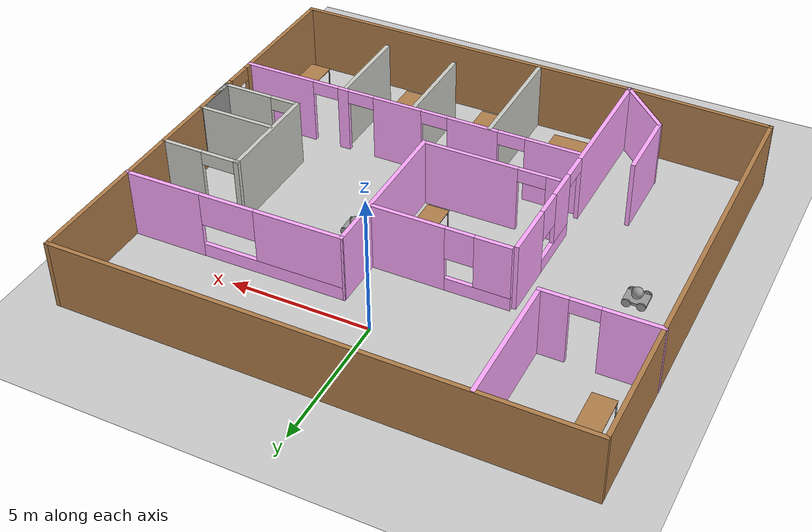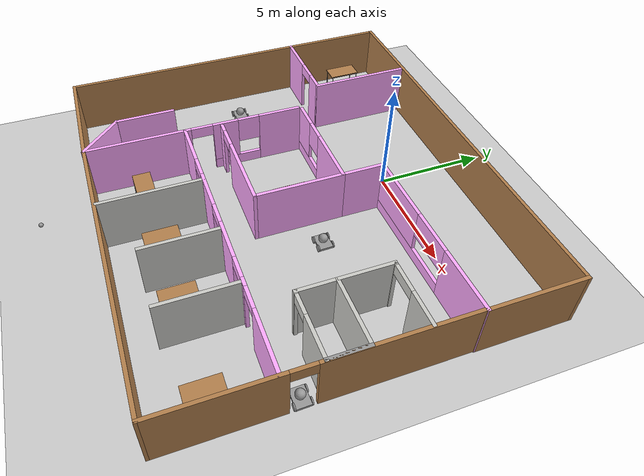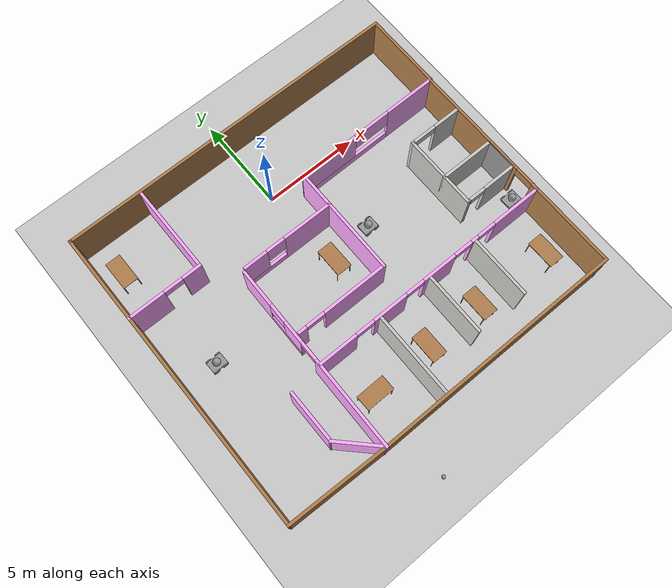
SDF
<sdf version="1.6">
 <world name="default">
  <plugin name="welcomebindu" filename="libwelcomebindu.so"/>
  <light name="sun" type="directional">
   <pose>0 0 10 0 -0 0</pose>
   <diffuse>0.8 0.8 0.8 1</diffuse>
   <specular>0.2 0.2 0.2 1</specular>
   <attenuation>
    <range>1000</range>
    <constant>0.9</constant>
    <linear>0.01</linear>
    <quadratic>0.001</quadratic>
   </attenuation>
   <direction>-0.5 0.1 -0.9</direction>
  </light>
  <model name="ground_plane">
   <static>1</static>
   <link name="link">
    <collision name="collision">
     <geometry><plane><normal>0 0 1</normal><size>100 100</size></plane></geometry>
     <surface>
      <contact><collide_bitmask>65535</collide_bitmask></contact>
      <friction><ode><mu>100</mu><mu2>50</mu2></ode></friction>
     </surface>
    </collision>
    <visual name="visual">
     <cast_shadows>0</cast_shadows>
     <geometry><plane><normal>0 0 1</normal><size>100 100</size></plane></geometry>
     <material>
      <script><uri>file://media/materials/scripts/gazebo.material</uri><name>Gazebo/Grey</name></script>
     </material>
    </visual>
   </link>
  </model>
  <gravity>0 0 -9.8</gravity>
  <magnetic_field>6e-06 2.3e-05 -4.2e-05</magnetic_field>
  <atmosphere type="adiabatic"/>
  <physics name="default_physics" default="0" type="ode">
   <max_step_size>0.001</max_step_size>
   <real_time_factor>1</real_time_factor>
   <real_time_update_rate>1000</real_time_update_rate>
  </physics>
  <scene><ambient>0.4 0.4 0.4 1</ambient><background>0.7 0.7 0.7 1</background><shadows>1</shadows></scene>
  <spherical_coordinates>
   <surface_model>EARTH_WGS84</surface_model>
   <latitude_deg>0</latitude_deg>
   <longitude_deg>0</longitude_deg>
   <elevation>0</elevation>
   <heading_deg>0</heading_deg>
  </spherical_coordinates>
  <model name="HumanoidRobot">
   <link name="link_0">
    <pose>0 0 -0.041667 0 -0 0</pose>
    <inertial>
     <mass>1</mass>
     <inertia>
      <ixx>0.166667</ixx>
      <ixy>0</ixy>
      <ixz>0</ixz>
      <iyy>0.166667</iyy>
      <iyz>0</iyz>
      <izz>0.166667</izz>
     </inertia>
    </inertial>
    <visual name="visual">
     <geometry><box><size>0.8 0.6 0.1</size></box></geometry>
     <material>
      <lighting>1</lighting>
      <script><uri>file://media/materials/scripts/gazebo.material</uri><name>Gazebo/Grey</name></script>
      <shader type="pixel"><normal_map>__default__</normal_map></shader>
      <ambient>0.3 0.3 0.3 1</ambient>
      <diffuse>0.7 0.7 0.7 1</diffuse>
      <specular>0.01 0.01 0.01 1</specular>
      <emissive>0 0 0 1</emissive>
     </material>
    </visual>
    <collision name="collision">
     <geometry><box><size>0.8 0.6 0.1</size></box></geometry>
     <surface>
      <friction>
       <ode><mu>1</mu><mu2>1</mu2><fdir1>0 0 0</fdir1><slip1>0</slip1><slip2>0</slip2></ode>
       <torsional>
        <coefficient>1</coefficient>
        <patch_radius>0</patch_radius>
        <surface_radius>0</surface_radius>
        <use_patch_radius>1</use_patch_radius>
        <ode><slip>0</slip></ode>
       </torsional>
      </friction>
      <bounce><restitution_coefficient>0</restitution_coefficient><threshold>1e+06</threshold></bounce>
      <contact>
       <collide_without_contact>0</collide_without_contact>
       <collide_without_contact_bitmask>1</collide_without_contact_bitmask>
       <collide_bitmask>1</collide_bitmask>
       <ode>
        <soft_cfm>0</soft_cfm>
        <soft_erp>0.2</soft_erp>
        <kp>1e+13</kp>
        <kd>1</kd>
        <max_vel>0.01</max_vel>
        <min_depth>0</min_depth>
       </ode>
       <bullet>
        <split_impulse>1</split_impulse>
        <split_impulse_penetration_threshold>-0.01</split_impulse_penetration_threshold>
        <soft_cfm>0</soft_cfm>
        <soft_erp>0.2</soft_erp>
        <kp>1e+13</kp>
        <kd>1</kd>
       </bullet>
      </contact>
     </surface>
    </collision>
   </link>
   <link name="link_1">
    <pose>-0.25 -0.325014 -0.041667 1.5707 -0 0</pose>
    <inertial>
     <mass>1</mass>
     <inertia><ixx>0.145833</ixx><ixy>0</ixy><ixz>0</ixz><iyy>0.145833</iyy><iyz>0</iyz><izz>0.125</izz></inertia>
    </inertial>
    <visual name="visual">
     <geometry><cylinder><radius>0.15</radius><length>0.05</length></cylinder></geometry>
     <material>
      <lighting>1</lighting>
      <script><uri>file://media/materials/scripts/gazebo.material</uri><name>Gazebo/Grey</name></script>
      <shader type="pixel"><normal_map>__default__</normal_map></shader>
      <ambient>0.3 0.3 0.3 1</ambient>
      <diffuse>0.7 0.7 0.7 1</diffuse>
      <specular>0.01 0.01 0.01 1</specular>
      <emissive>0 0 0 1</emissive>
     </material>
    </visual>
    <collision name="collision">
     <geometry><cylinder><radius>0.15</radius><length>0.05</length></cylinder></geometry>
     <surface>
      <friction>
       <ode><mu>1</mu><mu2>1</mu2><fdir1>0 0 0</fdir1><slip1>0</slip1><slip2>0</slip2></ode>
       <torsional>
        <coefficient>1</coefficient>
        <patch_radius>0</patch_radius>
        <surface_radius>0</surface_radius>
        <use_patch_radius>1</use_patch_radius>
        <ode><slip>0</slip></ode>
       </torsional>
      </friction>
      <bounce><restitution_coefficient>0</restitution_coefficient><threshold>1e+06</threshold></bounce>
      <contact>
       <collide_without_contact>0</collide_without_contact>
       <collide_without_contact_bitmask>1</collide_without_contact_bitmask>
       <collide_bitmask>1</collide_bitmask>
       <ode>
        <soft_cfm>0</soft_cfm>
        <soft_erp>0.2</soft_erp>
        <kp>1e+13</kp>
        <kd>1</kd>
        <max_vel>0.01</max_vel>
        <min_depth>0</min_depth>
       </ode>
       <bullet>
        <split_impulse>1</split_impulse>
        <split_impulse_penetration_threshold>-0.01</split_impulse_penetration_threshold>
        <soft_cfm>0</soft_cfm>
        <soft_erp>0.2</soft_erp>
        <kp>1e+13</kp>
        <kd>1</kd>
       </bullet>
      </contact>
     </surface>
    </collision>
   </link>
   <link name="link_1_clone">
    <pose>-0.25 0.325014 -0.041667 1.5707 -0 0</pose>
    <inertial>
     <mass>1</mass>
     <inertia><ixx>0.145833</ixx><ixy>0</ixy><ixz>0</ixz><iyy>0.145833</iyy><iyz>0</iyz><izz>0.125</izz></inertia>
    </inertial>
    <visual name="visual">
     <geometry><cylinder><radius>0.15</radius><length>0.05</length></cylinder></geometry>
     <material>
      <lighting>1</lighting>
      <script><uri>file://media/materials/scripts/gazebo.material</uri><name>Gazebo/Grey</name></script>
      <shader type="pixel"><normal_map>__default__</normal_map></shader>
      <ambient>0.3 0.3 0.3 1</ambient>
      <diffuse>0.7 0.7 0.7 1</diffuse>
      <specular>0.01 0.01 0.01 1</specular>
      <emissive>0 0 0 1</emissive>
     </material>
    </visual>
    <collision name="collision">
     <geometry><cylinder><radius>0.15</radius><length>0.05</length></cylinder></geometry>
     <surface>
      <friction>
       <ode><mu>1</mu><mu2>1</mu2><fdir1>0 0 0</fdir1><slip1>0</slip1><slip2>0</slip2></ode>
       <torsional>
        <coefficient>1</coefficient>
        <patch_radius>0</patch_radius>
        <surface_radius>0</surface_radius>
        <use_patch_radius>1</use_patch_radius>
        <ode><slip>0</slip></ode>
       </torsional>
      </friction>
      <bounce><restitution_coefficient>0</restitution_coefficient><threshold>1e+06</threshold></bounce>
      <contact>
       <collide_without_contact>0</collide_without_contact>
       <collide_without_contact_bitmask>1</collide_without_contact_bitmask>
       <collide_bitmask>1</collide_bitmask>
       <ode>
        <soft_cfm>0</soft_cfm>
        <soft_erp>0.2</soft_erp>
        <kp>1e+13</kp>
        <kd>1</kd>
        <max_vel>0.01</max_vel>
        <min_depth>0</min_depth>
       </ode>
       <bullet>
        <split_impulse>1</split_impulse>
        <split_impulse_penetration_threshold>-0.01</split_impulse_penetration_threshold>
        <soft_cfm>0</soft_cfm>
        <soft_erp>0.2</soft_erp>
        <kp>1e+13</kp>
        <kd>1</kd>
       </bullet>
      </contact>
     </surface>
    </collision>
   </link>
   <link name="link_1_clone_0">
    <pose>0.25 0.325014 -0.041667 1.5707 -0 0</pose>
    <inertial>
     <mass>1</mass>
     <inertia><ixx>0.145833</ixx><ixy>0</ixy><ixz>0</ixz><iyy>0.145833</iyy><iyz>0</iyz><izz>0.125</izz></inertia>
    </inertial>
    <visual name="visual">
     <geometry><cylinder><radius>0.15</radius><length>0.05</length></cylinder></geometry>
     <material>
      <lighting>1</lighting>
      <script><uri>file://media/materials/scripts/gazebo.material</uri><name>Gazebo/Grey</name></script>
      <shader type="pixel"><normal_map>__default__</normal_map></shader>
      <ambient>0.3 0.3 0.3 1</ambient>
      <diffuse>0.7 0.7 0.7 1</diffuse>
      <specular>0.01 0.01 0.01 1</specular>
      <emissive>0 0 0 1</emissive>
     </material>
    </visual>
    <collision name="collision">
     <geometry><cylinder><radius>0.15</radius><length>0.05</length></cylinder></geometry>
     <surface>
      <friction>
       <ode><mu>1</mu><mu2>1</mu2><fdir1>0 0 0</fdir1><slip1>0</slip1><slip2>0</slip2></ode>
       <torsional>
        <coefficient>1</coefficient>
        <patch_radius>0</patch_radius>
        <surface_radius>0</surface_radius>
        <use_patch_radius>1</use_patch_radius>
        <ode><slip>0</slip></ode>
       </torsional>
      </friction>
      <bounce><restitution_coefficient>0</restitution_coefficient><threshold>1e+06</threshold></bounce>
      <contact>
       <collide_without_contact>0</collide_without_contact>
       <collide_without_contact_bitmask>1</collide_without_contact_bitmask>
       <collide_bitmask>1</collide_bitmask>
       <ode>
        <soft_cfm>0</soft_cfm>
        <soft_erp>0.2</soft_erp>
        <kp>1e+13</kp>
        <kd>1</kd>
        <max_vel>0.01</max_vel>
        <min_depth>0</min_depth>
       </ode>
       <bullet>
        <split_impulse>1</split_impulse>
        <split_impulse_penetration_threshold>-0.01</split_impulse_penetration_threshold>
        <soft_cfm>0</soft_cfm>
        <soft_erp>0.2</soft_erp>
        <kp>1e+13</kp>
        <kd>1</kd>
       </bullet>
      </contact>
     </surface>
    </collision>
   </link>
   <link name="link_1_clone_1">
    <pose>0.25 -0.325014 -0.041667 1.5707 -0 0</pose>
    <inertial>
     <mass>1</mass>
     <inertia><ixx>0.145833</ixx><ixy>0</ixy><ixz>0</ixz><iyy>0.145833</iyy><iyz>0</iyz><izz>0.125</izz></inertia>
    </inertial>
    <visual name="visual">
     <geometry><cylinder><radius>0.15</radius><length>0.05</length></cylinder></geometry>
     <material>
      <lighting>1</lighting>
      <script><uri>file://media/materials/scripts/gazebo.material</uri><name>Gazebo/Grey</name></script>
      <shader type="pixel"><normal_map>__default__</normal_map></shader>
      <ambient>0.3 0.3 0.3 1</ambient>
      <diffuse>0.7 0.7 0.7 1</diffuse>
      <specular>0.01 0.01 0.01 1</specular>
      <emissive>0 0 0 1</emissive>
     </material>
    </visual>
    <collision name="collision">
     <geometry><cylinder><radius>0.15</radius><length>0.05</length></cylinder></geometry>
     <surface>
      <friction>
       <ode><mu>1</mu><mu2>1</mu2><fdir1>0 0 0</fdir1><slip1>0</slip1><slip2>0</slip2></ode>
       <torsional>
        <coefficient>1</coefficient>
        <patch_radius>0</patch_radius>
        <surface_radius>0</surface_radius>
        <use_patch_radius>1</use_patch_radius>
        <ode><slip>0</slip></ode>
       </torsional>
      </friction>
      <bounce><restitution_coefficient>0</restitution_coefficient><threshold>1e+06</threshold></bounce>
      <contact>
       <collide_without_contact>0</collide_without_contact>
       <collide_without_contact_bitmask>1</collide_without_contact_bitmask>
       <collide_bitmask>1</collide_bitmask>
       <ode>
        <soft_cfm>0</soft_cfm>
        <soft_erp>0.2</soft_erp>
        <kp>1e+13</kp>
        <kd>1</kd>
        <max_vel>0.01</max_vel>
        <min_depth>0</min_depth>
       </ode>
       <bullet>
        <split_impulse>1</split_impulse>
        <split_impulse_penetration_threshold>-0.01</split_impulse_penetration_threshold>
        <soft_cfm>0</soft_cfm>
        <soft_erp>0.2</soft_erp>
        <kp>1e+13</kp>
        <kd>1</kd>
       </bullet>
      </contact>
     </surface>
    </collision>
   </link>
   <link name="link_2">
    <pose>0 0 0.208333 0 -0 0</pose>
    <inertial>
     <mass>1</mass>
     <inertia><ixx>0.1</ixx><ixy>0</ixy><ixz>0</ixz><iyy>0.1</iyy><iyz>0</iyz><izz>0.1</izz></inertia>
    </inertial>
    <visual name="visual">
     <geometry><sphere><radius>0.2</radius></sphere></geometry>
     <material>
      <lighting>1</lighting>
      <script><uri>file://media/materials/scripts/gazebo.material</uri><name>Gazebo/Grey</name></script>
      <shader type="pixel"><normal_map>__default__</normal_map></shader>
      <ambient>0.3 0.3 0.3 1</ambient>
      <diffuse>0.7 0.7 0.7 1</diffuse>
      <specular>0.01 0.01 0.01 1</specular>
      <emissive>0 0 0 1</emissive>
     </material>
    </visual>
    <collision name="collision">
     <geometry><sphere><radius>0.2</radius></sphere></geometry>
     <surface>
      <friction>
       <ode><mu>1</mu><mu2>1</mu2><fdir1>0 0 0</fdir1><slip1>0</slip1><slip2>0</slip2></ode>
       <torsional>
        <coefficient>1</coefficient>
        <patch_radius>0</patch_radius>
        <surface_radius>0</surface_radius>
        <use_patch_radius>1</use_patch_radius>
        <ode><slip>0</slip></ode>
       </torsional>
      </friction>
      <bounce><restitution_coefficient>0</restitution_coefficient><threshold>1e+06</threshold></bounce>
      <contact>
       <collide_without_contact>0</collide_without_contact>
       <collide_without_contact_bitmask>1</collide_without_contact_bitmask>
       <collide_bitmask>1</collide_bitmask>
       <ode>
        <soft_cfm>0</soft_cfm>
        <soft_erp>0.2</soft_erp>
        <kp>1e+13</kp>
        <kd>1</kd>
        <max_vel>0.01</max_vel>
        <min_depth>0</min_depth>
       </ode>
       <bullet>
        <split_impulse>1</split_impulse>
        <split_impulse_penetration_threshold>-0.01</split_impulse_penetration_threshold>
        <soft_cfm>0</soft_cfm>
        <soft_erp>0.2</soft_erp>
        <kp>1e+13</kp>
        <kd>1</kd>
       </bullet>
      </contact>
     </surface>
    </collision>
   </link>
   <joint name="link_0_JOINT_0" type="revolute">
    <parent>link_0</parent>
    <child>link_1</child>
    <axis>
     <xyz>0 0 1</xyz>
     <use_parent_model_frame>0</use_parent_model_frame>
     <limit>
      <lower>-1.79769e+308</lower>
      <upper>1.79769e+308</upper>
      <effort>-1</effort>
      <velocity>-1</velocity>
     </limit>
     <dynamics>
      <spring_reference>0</spring_reference>
      <spring_stiffness>0</spring_stiffness>
      <damping>0</damping>
     </dynamics>
    </axis>
    <physics>
     <ode><limit><cfm>0</cfm><erp>0.2</erp></limit><suspension><cfm>0</cfm><erp>0.2</erp></suspension></ode>
    </physics>
   </joint>
   <joint name="link_0_JOINT_1" type="revolute">
    <parent>link_0</parent>
    <child>link_1_clone</child>
    <axis>
     <xyz>0 0 1</xyz>
     <use_parent_model_frame>0</use_parent_model_frame>
     <limit>
      <lower>-1.79769e+308</lower>
      <upper>1.79769e+308</upper>
      <effort>-1</effort>
      <velocity>-1</velocity>
     </limit>
     <dynamics>
      <spring_reference>0</spring_reference>
      <spring_stiffness>0</spring_stiffness>
      <damping>0</damping>
     </dynamics>
    </axis>
    <physics>
     <ode><limit><cfm>0</cfm><erp>0.2</erp></limit><suspension><cfm>0</cfm><erp>0.2</erp></suspension></ode>
    </physics>
   </joint>
   <joint name="link_0_JOINT_2" type="revolute">
    <parent>link_0</parent>
    <child>link_1_clone_0</child>
    <axis>
     <xyz>0 0 1</xyz>
     <use_parent_model_frame>0</use_parent_model_frame>
     <limit>
      <lower>-1.79769e+308</lower>
      <upper>1.79769e+308</upper>
      <effort>-1</effort>
      <velocity>-1</velocity>
     </limit>
     <dynamics>
      <spring_reference>0</spring_reference>
      <spring_stiffness>0</spring_stiffness>
      <damping>0</damping>
     </dynamics>
    </axis>
    <physics>
     <ode><limit><cfm>0</cfm><erp>0.2</erp></limit><suspension><cfm>0</cfm><erp>0.2</erp></suspension></ode>
    </physics>
   </joint>
   <joint name="link_0_JOINT_3" type="revolute">
    <parent>link_0</parent>
    <child>link_1_clone_1</child>
    <axis>
     <xyz>0 0 1</xyz>
     <use_parent_model_frame>0</use_parent_model_frame>
     <limit>
      <lower>-1.79769e+308</lower>
      <upper>1.79769e+308</upper>
      <effort>-1</effort>
      <velocity>-1</velocity>
     </limit>
     <dynamics>
      <spring_reference>0</spring_reference>
      <spring_stiffness>0</spring_stiffness>
      <damping>0</damping>
     </dynamics>
    </axis>
    <physics>
     <ode><limit><cfm>0</cfm><erp>0.2</erp></limit><suspension><cfm>0</cfm><erp>0.2</erp></suspension></ode>
    </physics>
   </joint>
   <joint name="link_0_JOINT_4" type="fixed">
    <parent>link_0</parent>
    <child>link_2</child>
    <physics>
     <ode><limit><cfm>0</cfm><erp>0.2</erp></limit><suspension><cfm>0</cfm><erp>0.2</erp></suspension></ode>
    </physics>
   </joint>
   <static>0</static>
   <pose>2.72252 -4.09584 0.191669 7e-06 -1e-05 0.026245</pose>
  </model>
  <model name="Building">
   <pose>0.26771 -4.76126 0 0 -0 0</pose>
   <link name="Wall_0">
    <pose>-3.89491 -3.07088 0 0 0 -1.57824</pose>
    <visual name="Wall_0_Visual_0">
     <pose>-3.9947 0 1.25 0 -0 0</pose>
     <geometry><box><size>1.99092 0.15 2.5</size></box></geometry>
     <material>
      <script><uri>file://media/materials/scripts/gazebo.material</uri><name>Gazebo/Grey</name></script>
      <ambient>1 0.666667 1 1</ambient>
     </material>
     <meta><layer>0</layer></meta>
    </visual>
    <collision name="Wall_0_Collision_0">
     <geometry><box><size>1.99092 0.15 2.5</size></box></geometry>
     <pose>-3.9947 0 1.25 0 -0 0</pose>
    </collision>
    <visual name="Wall_0_Visual_1">
     <pose>2.58886 0 1.25 0 -0 0</pose>
     <geometry><box><size>4.80261 0.15 2.5</size></box></geometry>
     <material>
      <script><uri>file://media/materials/scripts/gazebo.material</uri><name>Gazebo/Grey</name></script>
      <ambient>1 0.666667 1 1</ambient>
     </material>
     <meta><layer>0</layer></meta>
    </visual>
    <collision name="Wall_0_Collision_1">
     <geometry><box><size>4.80261 0.15 2.5</size></box></geometry>
     <pose>2.58886 0 1.25 0 -0 0</pose>
    </collision>
    <visual name="Wall_0_Visual_2">
     <pose>-1.90584 0 0.25 0 -0 0</pose>
     <geometry><box><size>2.18679 0.15 0.5</size></box></geometry>
     <material>
      <script><uri>file://media/materials/scripts/gazebo.material</uri><name>Gazebo/Grey</name></script>
      <ambient>1 0.666667 1 1</ambient>
     </material>
     <meta><layer>0</layer></meta>
    </visual>
    <collision name="Wall_0_Collision_2">
     <geometry><box><size>2.18679 0.15 0.5</size></box></geometry>
     <pose>-1.90584 0 0.25 0 -0 0</pose>
    </collision>
    <visual name="Wall_0_Visual_3">
     <pose>-1.40584 0 1.5 0 -0 0</pose>
     <geometry><box><size>1.18679 0.15 2</size></box></geometry>
     <material>
      <script><uri>file://media/materials/scripts/gazebo.material</uri><name>Gazebo/Grey</name></script>
      <ambient>1 0.666667 1 1</ambient>
     </material>
     <meta><layer>0</layer></meta>
    </visual>
    <collision name="Wall_0_Collision_3">
     <geometry><box><size>1.18679 0.15 2</size></box></geometry>
     <pose>-1.40584 0 1.5 0 -0 0</pose>
    </collision>
    <visual name="Wall_0_Visual_4">
     <pose>-2.49924 0 1.9 0 -0 0</pose>
     <geometry><box><size>1 0.15 1.2</size></box></geometry>
     <material>
      <script><uri>file://media/materials/scripts/gazebo.material</uri><name>Gazebo/Grey</name></script>
      <ambient>1 0.666667 1 1</ambient>
     </material>
     <meta><layer>0</layer></meta>
    </visual>
    <collision name="Wall_0_Collision_4">
     <geometry><box><size>1 0.15 1.2</size></box></geometry>
     <pose>-2.49924 0 1.9 0 -0 0</pose>
    </collision>
    <visual name="Wall_0_Visual_5">
     <pose>-0.312448 0 2.25 0 -0 0</pose>
     <geometry><box><size>1 0.15 0.5</size></box></geometry>
     <material>
      <script><uri>file://media/materials/scripts/gazebo.material</uri><name>Gazebo/Grey</name></script>
      <ambient>1 0.666667 1 1</ambient>
     </material>
     <meta><layer>0</layer></meta>
    </visual>
    <collision name="Wall_0_Collision_5">
     <geometry><box><size>1 0.15 0.5</size></box></geometry>
     <pose>-0.312448 0 2.25 0 -0 0</pose>
    </collision>
   </link>
   <link name="Wall_1">
    <collision name="Wall_1_Collision">
     <geometry><box><size>13.0918 0.15 2.5</size></box></geometry>
     <pose>0 0 1.25 0 -0 0</pose>
    </collision>
    <visual name="Wall_1_Visual">
     <pose>0 0 1.25 0 -0 0</pose>
     <geometry><box><size>13.0918 0.15 2.5</size></box></geometry>
     <material>
      <script><uri>file://media/materials/scripts/gazebo.material</uri><name>Gazebo/Wood</name></script>
      <ambient>1 1 1 1</ambient>
     </material>
     <meta><layer>0</layer></meta>
    </visual>
    <pose>2.5394 -7.9859 0 0 -0 0</pose>
   </link>
   <link name="Wall_10">
    <pose>2.57243 -3.52127 0 0 -0 0</pose>
    <visual name="Wall_10_Visual_0">
     <pose>-5.45325 0 1.25 0 -0 0</pose>
     <geometry><box><size>2.0935 0.15 2.5</size></box></geometry>
     <material>
      <script><uri>file://media/materials/scripts/gazebo.material</uri><name>Gazebo/Grey</name></script>
      <ambient>1 0.666667 1 1</ambient>
     </material>
     <meta><layer>0</layer></meta>
    </visual>
    <collision name="Wall_10_Collision_0">
     <geometry><box><size>2.0935 0.15 2.5</size></box></geometry>
     <pose>-5.45325 0 1.25 0 -0 0</pose>
    </collision>
    <visual name="Wall_10_Visual_1">
     <pose>-2.45836 0 1.25 0 -0 0</pose>
     <geometry><box><size>1.89627 0.15 2.5</size></box></geometry>
     <material>
      <script><uri>file://media/materials/scripts/gazebo.material</uri><name>Gazebo/Grey</name></script>
      <ambient>1 0.666667 1 1</ambient>
     </material>
     <meta><layer>0</layer></meta>
    </visual>
    <collision name="Wall_10_Collision_1">
     <geometry><box><size>1.89627 0.15 2.5</size></box></geometry>
     <pose>-2.45836 0 1.25 0 -0 0</pose>
    </collision>
    <visual name="Wall_10_Visual_2">
     <pose>0.424691 0 1.25 0 -0 0</pose>
     <geometry><box><size>1.86983 0.15 2.5</size></box></geometry>
     <material>
      <script><uri>file://media/materials/scripts/gazebo.material</uri><name>Gazebo/Grey</name></script>
      <ambient>1 0.666667 1 1</ambient>
     </material>
     <meta><layer>0</layer></meta>
    </visual>
    <collision name="Wall_10_Collision_2">
     <geometry><box><size>1.86983 0.15 2.5</size></box></geometry>
     <pose>0.424691 0 1.25 0 -0 0</pose>
    </collision>
    <visual name="Wall_10_Visual_3">
     <pose>2.56714 0 1.25 0 -0 0</pose>
     <geometry><box><size>0.415075 0.15 2.5</size></box></geometry>
     <material>
      <script><uri>file://media/materials/scripts/gazebo.material</uri><name>Gazebo/Grey</name></script>
      <ambient>1 0.666667 1 1</ambient>
     </material>
     <meta><layer>0</layer></meta>
    </visual>
    <collision name="Wall_10_Collision_3">
     <geometry><box><size>0.415075 0.15 2.5</size></box></geometry>
     <pose>2.56714 0 1.25 0 -0 0</pose>
    </collision>
    <visual name="Wall_10_Visual_4">
     <pose>5.13734 0 1.25 0 -0 0</pose>
     <geometry><box><size>2.72532 0.15 2.5</size></box></geometry>
     <material>
      <script><uri>file://media/materials/scripts/gazebo.material</uri><name>Gazebo/Grey</name></script>
      <ambient>1 0.666667 1 1</ambient>
     </material>
     <meta><layer>0</layer></meta>
    </visual>
    <collision name="Wall_10_Collision_4">
     <geometry><box><size>2.72532 0.15 2.5</size></box></geometry>
     <pose>5.13734 0 1.25 0 -0 0</pose>
    </collision>
    <visual name="Wall_10_Visual_5">
     <pose>-3.9065 0 2.25 0 -0 0</pose>
     <geometry><box><size>1 0.15 0.5</size></box></geometry>
     <material>
      <script><uri>file://media/materials/scripts/gazebo.material</uri><name>Gazebo/Grey</name></script>
      <ambient>1 0.666667 1 1</ambient>
     </material>
     <meta><layer>0</layer></meta>
    </visual>
    <collision name="Wall_10_Collision_5">
     <geometry><box><size>1 0.15 0.5</size></box></geometry>
     <pose>-3.9065 0 2.25 0 -0 0</pose>
    </collision>
    <visual name="Wall_10_Visual_6">
     <pose>-1.01022 0 2.25 0 -0 0</pose>
     <geometry><box><size>1 0.15 0.5</size></box></geometry>
     <material>
      <script><uri>file://media/materials/scripts/gazebo.material</uri><name>Gazebo/Grey</name></script>
      <ambient>1 0.666667 1 1</ambient>
     </material>
     <meta><layer>0</layer></meta>
    </visual>
    <collision name="Wall_10_Collision_6">
     <geometry><box><size>1 0.15 0.5</size></box></geometry>
     <pose>-1.01022 0 2.25 0 -0 0</pose>
    </collision>
    <visual name="Wall_10_Visual_7">
     <pose>1.8596 0 2.25 0 -0 0</pose>
     <geometry><box><size>1 0.15 0.5</size></box></geometry>
     <material>
      <script><uri>file://media/materials/scripts/gazebo.material</uri><name>Gazebo/Grey</name></script>
      <ambient>1 0.666667 1 1</ambient>
     </material>
     <meta><layer>0</layer></meta>
    </visual>
    <collision name="Wall_10_Collision_7">
     <geometry><box><size>1 0.15 0.5</size></box></geometry>
     <pose>1.8596 0 2.25 0 -0 0</pose>
    </collision>
    <visual name="Wall_10_Visual_8">
     <pose>3.27468 0 2.25 0 -0 0</pose>
     <geometry><box><size>1 0.15 0.5</size></box></geometry>
     <material>
      <script><uri>file://media/materials/scripts/gazebo.material</uri><name>Gazebo/Grey</name></script>
      <ambient>1 0.666667 1 1</ambient>
     </material>
     <meta><layer>0</layer></meta>
    </visual>
    <collision name="Wall_10_Collision_8">
     <geometry><box><size>1 0.15 0.5</size></box></geometry>
     <pose>3.27468 0 2.25 0 -0 0</pose>
    </collision>
   </link>
   <link name="Wall_12">
    <pose>7.56891 1.8886 0 0 -0 3.14159</pose>
    <visual name="Wall_12_Visual_0">
     <pose>-0.720538 0 1.25 0 -0 0</pose>
     <geometry><box><size>1.55892 0.15 2.5</size></box></geometry>
     <material>
      <script><uri>file://media/materials/scripts/gazebo.material</uri><name>Gazebo/CeilingTiled</name></script>
      <ambient>0.666667 0.666667 1 1</ambient>
     </material>
     <meta><layer>0</layer></meta>
    </visual>
    <collision name="Wall_12_Collision_0">
     <geometry><box><size>1.55892 0.15 2.5</size></box></geometry>
     <pose>-0.720538 0 1.25 0 -0 0</pose>
    </collision>
    <visual name="Wall_12_Visual_1">
     <pose>1.40446 0 1.25 0 -0 0</pose>
     <geometry><box><size>0.191076 0.15 2.5</size></box></geometry>
     <material>
      <script><uri>file://media/materials/scripts/gazebo.material</uri><name>Gazebo/CeilingTiled</name></script>
      <ambient>0.666667 0.666667 1 1</ambient>
     </material>
     <meta><layer>0</layer></meta>
    </visual>
    <collision name="Wall_12_Collision_1">
     <geometry><box><size>0.191076 0.15 2.5</size></box></geometry>
     <pose>1.40446 0 1.25 0 -0 0</pose>
    </collision>
    <visual name="Wall_12_Visual_2">
     <pose>0.683924 0 2.25 0 -0 0</pose>
     <geometry><box><size>1.25 0.15 0.5</size></box></geometry>
     <material>
      <script><uri>file://media/materials/scripts/gazebo.material</uri><name>Gazebo/CeilingTiled</name></script>
      <ambient>0.666667 0.666667 1 1</ambient>
     </material>
     <meta><layer>0</layer></meta>
    </visual>
    <collision name="Wall_12_Collision_2">
     <geometry><box><size>1.25 0.15 0.5</size></box></geometry>
     <pose>0.683924 0 2.25 0 -0 0</pose>
    </collision>
   </link>
   <link name="Wall_15">
    <collision name="Wall_15_Collision">
     <geometry><box><size>4 0.15 2.5</size></box></geometry>
     <pose>0 0 1.25 0 -0 0</pose>
    </collision>
    <visual name="Wall_15_Visual">
     <pose>0 0 1.25 0 -0 0</pose>
     <geometry><box><size>4 0.15 2.5</size></box></geometry>
     <material>
      <script><uri>file://media/materials/scripts/gazebo.material</uri><name>Gazebo/CeilingTiled</name></script>
      <ambient>0.666667 0.666667 1 1</ambient>
     </material>
     <meta><layer>0</layer></meta>
    </visual>
    <pose>6.14391 -0.036403 0 0 0 -1.5708</pose>
   </link>
   <link name="Wall_16">
    <pose>7.56891 -1.9614 0 0 -0 0</pose>
    <visual name="Wall_16_Visual_0">
     <pose>-1.40292 0 1.25 0 -0 0</pose>
     <geometry><box><size>0.194152 0.15 2.5</size></box></geometry>
     <material>
      <script><uri>file://media/materials/scripts/gazebo.material</uri><name>Gazebo/CeilingTiled</name></script>
      <ambient>0.666667 0.666667 1 1</ambient>
     </material>
     <meta><layer>0</layer></meta>
    </visual>
    <collision name="Wall_16_Collision_0">
     <geometry><box><size>0.194152 0.15 2.5</size></box></geometry>
     <pose>-1.40292 0 1.25 0 -0 0</pose>
    </collision>
    <visual name="Wall_16_Visual_1">
     <pose>0.547076 0 1.25 0 -0 0</pose>
     <geometry><box><size>1.90585 0.15 2.5</size></box></geometry>
     <material>
      <script><uri>file://media/materials/scripts/gazebo.material</uri><name>Gazebo/CeilingTiled</name></script>
      <ambient>0.666667 0.666667 1 1</ambient>
     </material>
     <meta><layer>0</layer></meta>
    </visual>
    <collision name="Wall_16_Collision_1">
     <geometry><box><size>1.90585 0.15 2.5</size></box></geometry>
     <pose>0.547076 0 1.25 0 -0 0</pose>
    </collision>
    <visual name="Wall_16_Visual_2">
     <pose>-0.855848 0 2.25 0 -0 0</pose>
     <geometry><box><size>0.9 0.15 0.5</size></box></geometry>
     <material>
      <script><uri>file://media/materials/scripts/gazebo.material</uri><name>Gazebo/CeilingTiled</name></script>
      <ambient>0.666667 0.666667 1 1</ambient>
     </material>
     <meta><layer>0</layer></meta>
    </visual>
    <collision name="Wall_16_Collision_2">
     <geometry><box><size>0.9 0.15 0.5</size></box></geometry>
     <pose>-0.855848 0 2.25 0 -0 0</pose>
    </collision>
   </link>
   <link name="Wall_17">
    <collision name="Wall_17_Collision">
     <geometry><box><size>1.75 0.15 2.5</size></box></geometry>
     <pose>0 0 1.25 0 -0 0</pose>
    </collision>
    <visual name="Wall_17_Visual">
     <pose>0 0 1.25 0 -0 0</pose>
     <geometry><box><size>1.75 0.15 2.5</size></box></geometry>
     <material>
      <script><uri>file://media/materials/scripts/gazebo.material</uri><name>Gazebo/Grey</name></script>
      <ambient>1 1 1 1</ambient>
     </material>
     <meta><layer>0</layer></meta>
    </visual>
    <pose>8.99391 -1.1614 0 0 -0 1.5708</pose>
   </link>
   <link name="Wall_18">
    <collision name="Wall_18_Collision">
     <geometry><box><size>3 0.15 2.5</size></box></geometry>
     <pose>0 0 1.25 0 -0 0</pose>
    </collision>
    <visual name="Wall_18_Visual">
     <pose>0 0 1.25 0 -0 0</pose>
     <geometry><box><size>3 0.15 2.5</size></box></geometry>
     <material>
      <script><uri>file://media/materials/scripts/gazebo.material</uri><name>Gazebo/CeilingTiled</name></script>
      <ambient>0.666667 0.666667 1 1</ambient>
     </material>
     <meta><layer>0</layer></meta>
    </visual>
    <pose>7.56891 -0.361403 0 0 -0 3.14159</pose>
   </link>
   <link name="Wall_2">
    <pose>9.01627 -2.06506 0 0 -0 1.56978</pose>
    <visual name="Wall_2_Visual_0">
     <pose>-3.568 0 1.25 0 -0 0</pose>
     <geometry><box><size>4.85569 0.15 2.5</size></box></geometry>
     <material>
      <script><uri>file://media/materials/scripts/gazebo.material</uri><name>Gazebo/Wood</name></script>
      <ambient>1 1 1 1</ambient>
     </material>
     <meta><layer>0</layer></meta>
    </visual>
    <collision name="Wall_2_Collision_0">
     <geometry><box><size>4.85569 0.15 2.5</size></box></geometry>
     <pose>-3.568 0 1.25 0 -0 0</pose>
    </collision>
    <visual name="Wall_2_Visual_1">
     <pose>2.92785 0 1.25 0 -0 0</pose>
     <geometry><box><size>6.136 0.15 2.5</size></box></geometry>
     <material>
      <script><uri>file://media/materials/scripts/gazebo.material</uri><name>Gazebo/Wood</name></script>
      <ambient>1 1 1 1</ambient>
     </material>
     <meta><layer>0</layer></meta>
    </visual>
    <collision name="Wall_2_Collision_1">
     <geometry><box><size>6.136 0.15 2.5</size></box></geometry>
     <pose>2.92785 0 1.25 0 -0 0</pose>
    </collision>
    <visual name="Wall_2_Visual_2">
     <pose>-0.640156 0 2.25 0 -0 0</pose>
     <geometry><box><size>1 0.15 0.5</size></box></geometry>
     <material>
      <script><uri>file://media/materials/scripts/gazebo.material</uri><name>Gazebo/Wood</name></script>
      <ambient>1 1 1 1</ambient>
     </material>
     <meta><layer>0</layer></meta>
    </visual>
    <collision name="Wall_2_Collision_2">
     <geometry><box><size>1 0.15 0.5</size></box></geometry>
     <pose>-0.640156 0 2.25 0 -0 0</pose>
    </collision>
   </link>
   <link name="Wall_21">
    <collision name="Wall_21_Collision">
     <geometry><box><size>4.5 0.15 2.5</size></box></geometry>
     <pose>0 0 1.25 0 -0 0</pose>
    </collision>
    <visual name="Wall_21_Visual">
     <pose>0 0 1.25 0 -0 0</pose>
     <geometry><box><size>4.5 0.15 2.5</size></box></geometry>
     <material>
      <script><uri>file://media/materials/scripts/gazebo.material</uri><name>Gazebo/CeilingTiled</name></script>
      <ambient>1 0.666667 1 1</ambient>
     </material>
     <meta><layer>0</layer></meta>
    </visual>
    <pose>-0.507784 -5.74646 0 0 0 -1.5708</pose>
   </link>
   <link name="Wall_23">
    <collision name="Wall_23_Collision">
     <geometry><box><size>3.25 0.15 2.5</size></box></geometry>
     <pose>0 0 1.25 0 -0 0</pose>
    </collision>
    <visual name="Wall_23_Visual">
     <pose>0 0 1.25 0 -0 0</pose>
     <geometry><box><size>3.25 0.15 2.5</size></box></geometry>
     <material>
      <script><uri>file://media/materials/scripts/gazebo.material</uri><name>Gazebo/CeilingTiled</name></script>
      <ambient>1 0.666667 1 1</ambient>
     </material>
     <meta><layer>0</layer></meta>
    </visual>
    <pose>2.39271 -5.21989 0 0 0 -1.5708</pose>
   </link>
   <link name="Wall_25">
    <collision name="Wall_25_Collision">
     <geometry><box><size>3.25 0.15 2.5</size></box></geometry>
     <pose>0 0 1.25 0 -0 0</pose>
    </collision>
    <visual name="Wall_25_Visual">
     <pose>0 0 1.25 0 -0 0</pose>
     <geometry><box><size>3.25 0.15 2.5</size></box></geometry>
     <material>
      <script><uri>file://media/materials/scripts/gazebo.material</uri><name>Gazebo/CeilingTiled</name></script>
      <ambient>1 0.666667 1 1</ambient>
     </material>
     <meta><layer>0</layer></meta>
    </visual>
    <pose>5.11344 -5.21592 0 0 0 -1.5708</pose>
   </link>
   <link name="Wall_27">
    <collision name="Wall_27_Collision">
     <geometry><box><size>4.25 0.15 2.5</size></box></geometry>
     <pose>0 0 1.25 0 -0 0</pose>
    </collision>
    <visual name="Wall_27_Visual">
     <pose>0 0 1.25 0 -0 0</pose>
     <geometry><box><size>4.25 0.15 2.5</size></box></geometry>
     <material>
      <script><uri>file://media/materials/scripts/gazebo.material</uri><name>Gazebo/Wood</name></script>
      <ambient>1 1 1 1</ambient>
     </material>
     <meta><layer>0</layer></meta>
    </visual>
    <pose>9.05284 5.96697 0 0 -0 1.5708</pose>
   </link>
   <link name="Wall_28">
    <collision name="Wall_28_Collision">
     <geometry><box><size>18.25 0.15 2.5</size></box></geometry>
     <pose>0 0 1.25 0 -0 0</pose>
    </collision>
    <visual name="Wall_28_Visual">
     <pose>0 0 1.25 0 -0 0</pose>
     <geometry><box><size>18.25 0.15 2.5</size></box></geometry>
     <material>
      <script><uri>file://media/materials/scripts/gazebo.material</uri><name>Gazebo/Wood</name></script>
      <ambient>1 1 1 1</ambient>
     </material>
     <meta><layer>0</layer></meta>
    </visual>
    <pose>0.002842 8.01697 0 0 -0 3.14159</pose>
   </link>
   <link name="Wall_3">
    <pose>5.09725 3.88056 0 0 0 -3.13239</pose>
    <visual name="Wall_3_Visual_0">
     <pose>-2.60316 0 1.25 0 -0 0</pose>
     <geometry><box><size>2.85486 0.15 2.5</size></box></geometry>
     <material>
      <script><uri>file://media/materials/scripts/gazebo.material</uri><name>Gazebo/Grey</name></script>
      <ambient>1 0.666667 1 1</ambient>
     </material>
     <meta><layer>0</layer></meta>
    </visual>
    <collision name="Wall_3_Collision_0">
     <geometry><box><size>2.85486 0.15 2.5</size></box></geometry>
     <pose>-2.60316 0 1.25 0 -0 0</pose>
    </collision>
    <visual name="Wall_3_Visual_1">
     <pose>1.42743 0 0.25 0 -0 0</pose>
     <geometry><box><size>5.20633 0.15 0.5</size></box></geometry>
     <material>
      <script><uri>file://media/materials/scripts/gazebo.material</uri><name>Gazebo/Grey</name></script>
      <ambient>1 0.666667 1 1</ambient>
     </material>
     <meta><layer>0</layer></meta>
    </visual>
    <collision name="Wall_3_Collision_1">
     <geometry><box><size>5.20633 0.15 0.5</size></box></geometry>
     <pose>1.42743 0 0.25 0 -0 0</pose>
    </collision>
    <visual name="Wall_3_Visual_2">
     <pose>2.42743 0 1.5 0 -0 0</pose>
     <geometry><box><size>3.20633 0.15 2</size></box></geometry>
     <material>
      <script><uri>file://media/materials/scripts/gazebo.material</uri><name>Gazebo/Grey</name></script>
      <ambient>1 0.666667 1 1</ambient>
     </material>
     <meta><layer>0</layer></meta>
    </visual>
    <collision name="Wall_3_Collision_2">
     <geometry><box><size>3.20633 0.15 2</size></box></geometry>
     <pose>2.42743 0 1.5 0 -0 0</pose>
    </collision>
    <visual name="Wall_3_Visual_3">
     <pose>-0.175731 0 1.9 0 -0 0</pose>
     <geometry><box><size>2 0.15 1.2</size></box></geometry>
     <material>
      <script><uri>file://media/materials/scripts/gazebo.material</uri><name>Gazebo/Grey</name></script>
      <ambient>1 0.666667 1 1</ambient>
     </material>
     <meta><layer>0</layer></meta>
    </visual>
    <collision name="Wall_3_Collision_3">
     <geometry><box><size>2 0.15 1.2</size></box></geometry>
     <pose>-0.175731 0 1.9 0 -0 0</pose>
    </collision>
   </link>
   <link name="Wall_32">
    <collision name="Wall_32_Collision">
     <geometry><box><size>16 0.15 2.5</size></box></geometry>
     <pose>0 0 1.25 0 -0 0</pose>
    </collision>
    <visual name="Wall_32_Visual">
     <pose>0 0 1.25 0 -0 0</pose>
     <geometry><box><size>16 0.15 2.5</size></box></geometry>
     <material>
      <script><uri>file://media/materials/scripts/gazebo.material</uri><name>Gazebo/Wood</name></script>
      <ambient>1 1 1 1</ambient>
     </material>
     <meta><layer>0</layer></meta>
    </visual>
    <pose>-9.04716 0.091965 0 0 0 -1.5708</pose>
   </link>
   <link name="Wall_33">
    <collision name="Wall_33_Collision">
     <geometry><box><size>5.26795 0.15 2.5</size></box></geometry>
     <pose>0 0 1.25 0 -0 0</pose>
    </collision>
    <visual name="Wall_33_Visual">
     <pose>0 0 1.25 0 -0 0</pose>
     <geometry><box><size>5.26795 0.15 2.5</size></box></geometry>
     <material>
      <script><uri>file://media/materials/scripts/gazebo.material</uri><name>Gazebo/Wood</name></script>
      <ambient>1 1 1 1</ambient>
     </material>
     <meta><layer>0</layer></meta>
    </visual>
    <pose>-6.48932 -7.90947 0 0 0 -0.029873</pose>
   </link>
   <link name="Wall_34">
    <collision name="Wall_34_Collision">
     <geometry><box><size>2.5 0.15 2.5</size></box></geometry>
     <pose>0 0 1.25 0 -0 0</pose>
    </collision>
    <visual name="Wall_34_Visual">
     <pose>0 0 1.25 0 -0 0</pose>
     <geometry><box><size>2.5 0.15 2.5</size></box></geometry>
     <material>
      <script><uri>file://media/materials/scripts/gazebo.material</uri><name>Gazebo/Grey</name></script>
      <ambient>1 0.666667 1 1</ambient>
     </material>
     <meta><layer>0</layer></meta>
    </visual>
    <pose>-4.76234 -7.15505 0 0 -0 2.35619</pose>
   </link>
   <link name="Wall_35">
    <collision name="Wall_35_Collision">
     <geometry><box><size>2.75 0.15 2.5</size></box></geometry>
     <pose>0 0 1.25 0 -0 0</pose>
    </collision>
    <visual name="Wall_35_Visual">
     <pose>0 0 1.25 0 -0 0</pose>
     <geometry><box><size>2.75 0.15 2.5</size></box></geometry>
     <material>
      <script><uri>file://media/materials/scripts/gazebo.material</uri><name>Gazebo/Grey</name></script>
      <ambient>1 0.666667 1 1</ambient>
     </material>
     <meta><layer>0</layer></meta>
    </visual>
    <pose>-5.59319 -5.0242 0 0 -0 1.5708</pose>
   </link>
   <link name="Wall_37">
    <pose>-7.12837 3.3843 0 0 -0 0</pose>
    <visual name="Wall_37_Visual_0">
     <pose>-1.01948 0 1.25 0 -0 0</pose>
     <geometry><box><size>1.96104 0.15 2.5</size></box></geometry>
     <material>
      <script><uri>file://media/materials/scripts/gazebo.material</uri><name>Gazebo/Grey</name></script>
      <ambient>1 0.666667 1 1</ambient>
     </material>
     <meta><layer>0</layer></meta>
    </visual>
    <collision name="Wall_37_Collision_0">
     <geometry><box><size>1.96104 0.15 2.5</size></box></geometry>
     <pose>-1.01948 0 1.25 0 -0 0</pose>
    </collision>
    <visual name="Wall_37_Visual_1">
     <pose>1.48052 0 1.25 0 -0 0</pose>
     <geometry><box><size>1.03896 0.15 2.5</size></box></geometry>
     <material>
      <script><uri>file://media/materials/scripts/gazebo.material</uri><name>Gazebo/Grey</name></script>
      <ambient>1 0.666667 1 1</ambient>
     </material>
     <meta><layer>0</layer></meta>
    </visual>
    <collision name="Wall_37_Collision_1">
     <geometry><box><size>1.03896 0.15 2.5</size></box></geometry>
     <pose>1.48052 0 1.25 0 -0 0</pose>
    </collision>
    <visual name="Wall_37_Visual_2">
     <pose>0.461038 0 2.25 0 -0 0</pose>
     <geometry><box><size>1 0.15 0.5</size></box></geometry>
     <material>
      <script><uri>file://media/materials/scripts/gazebo.material</uri><name>Gazebo/Grey</name></script>
      <ambient>1 0.666667 1 1</ambient>
     </material>
     <meta><layer>0</layer></meta>
    </visual>
    <collision name="Wall_37_Collision_2">
     <geometry><box><size>1 0.15 0.5</size></box></geometry>
     <pose>0.461038 0 2.25 0 -0 0</pose>
    </collision>
   </link>
   <link name="Wall_38">
    <collision name="Wall_38_Collision">
     <geometry><box><size>4.75 0.15 2.5</size></box></geometry>
     <pose>0 0 1.25 0 -0 0</pose>
    </collision>
    <visual name="Wall_38_Visual">
     <pose>0 0 1.25 0 -0 0</pose>
     <geometry><box><size>4.75 0.15 2.5</size></box></geometry>
     <material>
      <script><uri>file://media/materials/scripts/gazebo.material</uri><name>Gazebo/Grey</name></script>
      <ambient>1 0.666667 1 1</ambient>
     </material>
     <meta><layer>0</layer></meta>
    </visual>
    <pose>-5.20337 5.6843 0 0 -0 1.5708</pose>
   </link>
   <link name="Wall_4">
    <collision name="Wall_4_Collision">
     <geometry><box><size>2 0.15 2.5</size></box></geometry>
     <pose>0 0 1.25 0 -0 0</pose>
    </collision>
    <visual name="Wall_4_Visual">
     <pose>0 0 1.25 0 -0 0</pose>
     <geometry><box><size>2 0.15 2.5</size></box></geometry>
     <material>
      <script><uri>file://media/materials/scripts/gazebo.material</uri><name>Gazebo/Grey</name></script>
      <ambient>1 0.666667 1 1</ambient>
     </material>
     <meta><layer>0</layer></meta>
    </visual>
    <pose>1.14166 2.91915 0 0 0 -1.5708</pose>
   </link>
   <link name="Wall_5">
    <pose>-1.28334 1.99415 0 0 -0 3.14159</pose>
    <visual name="Wall_5_Visual_0">
     <pose>-1.1425 0 1.25 0 -0 0</pose>
     <geometry><box><size>2.715 0.15 2.5</size></box></geometry>
     <material>
      <script><uri>file://media/materials/scripts/gazebo.material</uri><name>Gazebo/Grey</name></script>
      <ambient>1 0.666667 1 1</ambient>
     </material>
     <meta><layer>0</layer></meta>
    </visual>
    <collision name="Wall_5_Collision_0">
     <geometry><box><size>2.715 0.15 2.5</size></box></geometry>
     <pose>-1.1425 0 1.25 0 -0 0</pose>
    </collision>
    <visual name="Wall_5_Visual_1">
     <pose>1.3575 0 0.25 0 -0 0</pose>
     <geometry><box><size>2.285 0.15 0.5</size></box></geometry>
     <material>
      <script><uri>file://media/materials/scripts/gazebo.material</uri><name>Gazebo/Grey</name></script>
      <ambient>1 0.666667 1 1</ambient>
     </material>
     <meta><layer>0</layer></meta>
    </visual>
    <collision name="Wall_5_Collision_1">
     <geometry><box><size>2.285 0.15 0.5</size></box></geometry>
     <pose>1.3575 0 0.25 0 -0 0</pose>
    </collision>
    <visual name="Wall_5_Visual_2">
     <pose>1.8575 0 1.5 0 -0 0</pose>
     <geometry><box><size>1.285 0.15 2</size></box></geometry>
     <material>
      <script><uri>file://media/materials/scripts/gazebo.material</uri><name>Gazebo/Grey</name></script>
      <ambient>1 0.666667 1 1</ambient>
     </material>
     <meta><layer>0</layer></meta>
    </visual>
    <collision name="Wall_5_Collision_2">
     <geometry><box><size>1.285 0.15 2</size></box></geometry>
     <pose>1.8575 0 1.5 0 -0 0</pose>
    </collision>
    <visual name="Wall_5_Visual_3">
     <pose>0.715001 0 1.9 0 -0 0</pose>
     <geometry><box><size>1 0.15 1.2</size></box></geometry>
     <material>
      <script><uri>file://media/materials/scripts/gazebo.material</uri><name>Gazebo/Grey</name></script>
      <ambient>1 0.666667 1 1</ambient>
     </material>
     <meta><layer>0</layer></meta>
    </visual>
    <collision name="Wall_5_Collision_3">
     <geometry><box><size>1 0.15 1.2</size></box></geometry>
     <pose>0.715001 0 1.9 0 -0 0</pose>
    </collision>
   </link>
   <link name="Wall_7">
    <collision name="Wall_7_Collision">
     <geometry><box><size>4 0.15 2.5</size></box></geometry>
     <pose>0 0 1.25 0 -0 0</pose>
    </collision>
    <visual name="Wall_7_Visual">
     <pose>0 0 1.25 0 -0 0</pose>
     <geometry><box><size>4 0.15 2.5</size></box></geometry>
     <material>
      <script><uri>file://media/materials/scripts/gazebo.material</uri><name>Gazebo/Grey</name></script>
      <ambient>1 0.666667 1 1</ambient>
     </material>
     <meta><layer>0</layer></meta>
    </visual>
    <pose>1.14166 0.069149 0 0 0 -1.5708</pose>
   </link>
   <link name="Wall_8">
    <pose>-1.28334 -1.85585 0 0 -0 3.14159</pose>
    <visual name="Wall_8_Visual_0">
     <pose>-0.743815 0 1.25 0 -0 0</pose>
     <geometry><box><size>3.51237 0.15 2.5</size></box></geometry>
     <material>
      <script><uri>file://media/materials/scripts/gazebo.material</uri><name>Gazebo/Grey</name></script>
      <ambient>1 0.666667 1 1</ambient>
     </material>
     <meta><layer>0</layer></meta>
    </visual>
    <collision name="Wall_8_Collision_0">
     <geometry><box><size>3.51237 0.15 2.5</size></box></geometry>
     <pose>-0.743815 0 1.25 0 -0 0</pose>
    </collision>
    <visual name="Wall_8_Visual_1">
     <pose>2.25618 0 1.25 0 -0 0</pose>
     <geometry><box><size>0.48763 0.15 2.5</size></box></geometry>
     <material>
      <script><uri>file://media/materials/scripts/gazebo.material</uri><name>Gazebo/Grey</name></script>
      <ambient>1 0.666667 1 1</ambient>
     </material>
     <meta><layer>0</layer></meta>
    </visual>
    <collision name="Wall_8_Collision_1">
     <geometry><box><size>0.48763 0.15 2.5</size></box></geometry>
     <pose>2.25618 0 1.25 0 -0 0</pose>
    </collision>
    <visual name="Wall_8_Visual_2">
     <pose>1.51237 0 2.25 0 -0 0</pose>
     <geometry><box><size>1 0.15 0.5</size></box></geometry>
     <material>
      <script><uri>file://media/materials/scripts/gazebo.material</uri><name>Gazebo/Grey</name></script>
      <ambient>1 0.666667 1 1</ambient>
     </material>
     <meta><layer>0</layer></meta>
    </visual>
    <collision name="Wall_8_Collision_2">
     <geometry><box><size>1 0.15 0.5</size></box></geometry>
     <pose>1.51237 0 2.25 0 -0 0</pose>
    </collision>
   </link>
   <static>1</static>
  </model>
  <model name="HumanoidRobot_0">
   <link name="link_0">
    <pose>0 0 -0.041667 0 -0 0</pose>
    <inertial>
     <mass>1</mass>
     <inertia>
      <ixx>0.166667</ixx>
      <ixy>0</ixy>
      <ixz>0</ixz>
      <iyy>0.166667</iyy>
      <iyz>0</iyz>
      <izz>0.166667</izz>
     </inertia>
    </inertial>
    <visual name="visual">
     <geometry><box><size>0.8 0.6 0.1</size></box></geometry>
     <material>
      <lighting>1</lighting>
      <script><uri>file://media/materials/scripts/gazebo.material</uri><name>Gazebo/Grey</name></script>
      <shader type="pixel"><normal_map>__default__</normal_map></shader>
      <ambient>0.3 0.3 0.3 1</ambient>
      <diffuse>0.7 0.7 0.7 1</diffuse>
      <specular>0.01 0.01 0.01 1</specular>
      <emissive>0 0 0 1</emissive>
     </material>
    </visual>
    <collision name="collision">
     <geometry><box><size>0.8 0.6 0.1</size></box></geometry>
     <surface>
      <friction>
       <ode><mu>1</mu><mu2>1</mu2><fdir1>0 0 0</fdir1><slip1>0</slip1><slip2>0</slip2></ode>
       <torsional>
        <coefficient>1</coefficient>
        <patch_radius>0</patch_radius>
        <surface_radius>0</surface_radius>
        <use_patch_radius>1</use_patch_radius>
        <ode><slip>0</slip></ode>
       </torsional>
      </friction>
      <bounce><restitution_coefficient>0</restitution_coefficient><threshold>1e+06</threshold></bounce>
      <contact>
       <collide_without_contact>0</collide_without_contact>
       <collide_without_contact_bitmask>1</collide_without_contact_bitmask>
       <collide_bitmask>1</collide_bitmask>
       <ode>
        <soft_cfm>0</soft_cfm>
        <soft_erp>0.2</soft_erp>
        <kp>1e+13</kp>
        <kd>1</kd>
        <max_vel>0.01</max_vel>
        <min_depth>0</min_depth>
       </ode>
       <bullet>
        <split_impulse>1</split_impulse>
        <split_impulse_penetration_threshold>-0.01</split_impulse_penetration_threshold>
        <soft_cfm>0</soft_cfm>
        <soft_erp>0.2</soft_erp>
        <kp>1e+13</kp>
        <kd>1</kd>
       </bullet>
      </contact>
     </surface>
    </collision>
   </link>
   <link name="link_1">
    <pose>-0.25 -0.325014 -0.041667 1.5707 -0 0</pose>
    <inertial>
     <mass>1</mass>
     <inertia><ixx>0.145833</ixx><ixy>0</ixy><ixz>0</ixz><iyy>0.145833</iyy><iyz>0</iyz><izz>0.125</izz></inertia>
    </inertial>
    <visual name="visual">
     <geometry><cylinder><radius>0.15</radius><length>0.05</length></cylinder></geometry>
     <material>
      <lighting>1</lighting>
      <script><uri>file://media/materials/scripts/gazebo.material</uri><name>Gazebo/Grey</name></script>
      <shader type="pixel"><normal_map>__default__</normal_map></shader>
      <ambient>0.3 0.3 0.3 1</ambient>
      <diffuse>0.7 0.7 0.7 1</diffuse>
      <specular>0.01 0.01 0.01 1</specular>
      <emissive>0 0 0 1</emissive>
     </material>
    </visual>
    <collision name="collision">
     <geometry><cylinder><radius>0.15</radius><length>0.05</length></cylinder></geometry>
     <surface>
      <friction>
       <ode><mu>1</mu><mu2>1</mu2><fdir1>0 0 0</fdir1><slip1>0</slip1><slip2>0</slip2></ode>
       <torsional>
        <coefficient>1</coefficient>
        <patch_radius>0</patch_radius>
        <surface_radius>0</surface_radius>
        <use_patch_radius>1</use_patch_radius>
        <ode><slip>0</slip></ode>
       </torsional>
      </friction>
      <bounce><restitution_coefficient>0</restitution_coefficient><threshold>1e+06</threshold></bounce>
      <contact>
       <collide_without_contact>0</collide_without_contact>
       <collide_without_contact_bitmask>1</collide_without_contact_bitmask>
       <collide_bitmask>1</collide_bitmask>
       <ode>
        <soft_cfm>0</soft_cfm>
        <soft_erp>0.2</soft_erp>
        <kp>1e+13</kp>
        <kd>1</kd>
        <max_vel>0.01</max_vel>
        <min_depth>0</min_depth>
       </ode>
       <bullet>
        <split_impulse>1</split_impulse>
        <split_impulse_penetration_threshold>-0.01</split_impulse_penetration_threshold>
        <soft_cfm>0</soft_cfm>
        <soft_erp>0.2</soft_erp>
        <kp>1e+13</kp>
        <kd>1</kd>
       </bullet>
      </contact>
     </surface>
    </collision>
   </link>
   <link name="link_1_clone">
    <pose>-0.25 0.325014 -0.041667 1.5707 -0 0</pose>
    <inertial>
     <mass>1</mass>
     <inertia><ixx>0.145833</ixx><ixy>0</ixy><ixz>0</ixz><iyy>0.145833</iyy><iyz>0</iyz><izz>0.125</izz></inertia>
    </inertial>
    <visual name="visual">
     <geometry><cylinder><radius>0.15</radius><length>0.05</length></cylinder></geometry>
     <material>
      <lighting>1</lighting>
      <script><uri>file://media/materials/scripts/gazebo.material</uri><name>Gazebo/Grey</name></script>
      <shader type="pixel"><normal_map>__default__</normal_map></shader>
      <ambient>0.3 0.3 0.3 1</ambient>
      <diffuse>0.7 0.7 0.7 1</diffuse>
      <specular>0.01 0.01 0.01 1</specular>
      <emissive>0 0 0 1</emissive>
     </material>
    </visual>
    <collision name="collision">
     <geometry><cylinder><radius>0.15</radius><length>0.05</length></cylinder></geometry>
     <surface>
      <friction>
       <ode><mu>1</mu><mu2>1</mu2><fdir1>0 0 0</fdir1><slip1>0</slip1><slip2>0</slip2></ode>
       <torsional>
        <coefficient>1</coefficient>
        <patch_radius>0</patch_radius>
        <surface_radius>0</surface_radius>
        <use_patch_radius>1</use_patch_radius>
        <ode><slip>0</slip></ode>
       </torsional>
      </friction>
      <bounce><restitution_coefficient>0</restitution_coefficient><threshold>1e+06</threshold></bounce>
      <contact>
       <collide_without_contact>0</collide_without_contact>
       <collide_without_contact_bitmask>1</collide_without_contact_bitmask>
       <collide_bitmask>1</collide_bitmask>
       <ode>
        <soft_cfm>0</soft_cfm>
        <soft_erp>0.2</soft_erp>
        <kp>1e+13</kp>
        <kd>1</kd>
        <max_vel>0.01</max_vel>
        <min_depth>0</min_depth>
       </ode>
       <bullet>
        <split_impulse>1</split_impulse>
        <split_impulse_penetration_threshold>-0.01</split_impulse_penetration_threshold>
        <soft_cfm>0</soft_cfm>
        <soft_erp>0.2</soft_erp>
        <kp>1e+13</kp>
        <kd>1</kd>
       </bullet>
      </contact>
     </surface>
    </collision>
   </link>
   <link name="link_1_clone_0">
    <pose>0.25 0.325014 -0.041667 1.5707 -0 0</pose>
    <inertial>
     <mass>1</mass>
     <inertia><ixx>0.145833</ixx><ixy>0</ixy><ixz>0</ixz><iyy>0.145833</iyy><iyz>0</iyz><izz>0.125</izz></inertia>
    </inertial>
    <visual name="visual">
     <geometry><cylinder><radius>0.15</radius><length>0.05</length></cylinder></geometry>
     <material>
      <lighting>1</lighting>
      <script><uri>file://media/materials/scripts/gazebo.material</uri><name>Gazebo/Grey</name></script>
      <shader type="pixel"><normal_map>__default__</normal_map></shader>
      <ambient>0.3 0.3 0.3 1</ambient>
      <diffuse>0.7 0.7 0.7 1</diffuse>
      <specular>0.01 0.01 0.01 1</specular>
      <emissive>0 0 0 1</emissive>
     </material>
    </visual>
    <collision name="collision">
     <geometry><cylinder><radius>0.15</radius><length>0.05</length></cylinder></geometry>
     <surface>
      <friction>
       <ode><mu>1</mu><mu2>1</mu2><fdir1>0 0 0</fdir1><slip1>0</slip1><slip2>0</slip2></ode>
       <torsional>
        <coefficient>1</coefficient>
        <patch_radius>0</patch_radius>
        <surface_radius>0</surface_radius>
        <use_patch_radius>1</use_patch_radius>
        <ode><slip>0</slip></ode>
       </torsional>
      </friction>
      <bounce><restitution_coefficient>0</restitution_coefficient><threshold>1e+06</threshold></bounce>
      <contact>
       <collide_without_contact>0</collide_without_contact>
       <collide_without_contact_bitmask>1</collide_without_contact_bitmask>
       <collide_bitmask>1</collide_bitmask>
       <ode>
        <soft_cfm>0</soft_cfm>
        <soft_erp>0.2</soft_erp>
        <kp>1e+13</kp>
        <kd>1</kd>
        <max_vel>0.01</max_vel>
        <min_depth>0</min_depth>
       </ode>
       <bullet>
        <split_impulse>1</split_impulse>
        <split_impulse_penetration_threshold>-0.01</split_impulse_penetration_threshold>
        <soft_cfm>0</soft_cfm>
        <soft_erp>0.2</soft_erp>
        <kp>1e+13</kp>
        <kd>1</kd>
       </bullet>
      </contact>
     </surface>
    </collision>
   </link>
   <link name="link_1_clone_1">
    <pose>0.25 -0.325014 -0.041667 1.5707 -0 0</pose>
    <inertial>
     <mass>1</mass>
     <inertia><ixx>0.145833</ixx><ixy>0</ixy><ixz>0</ixz><iyy>0.145833</iyy><iyz>0</iyz><izz>0.125</izz></inertia>
    </inertial>
    <visual name="visual">
     <geometry><cylinder><radius>0.15</radius><length>0.05</length></cylinder></geometry>
     <material>
      <lighting>1</lighting>
      <script><uri>file://media/materials/scripts/gazebo.material</uri><name>Gazebo/Grey</name></script>
      <shader type="pixel"><normal_map>__default__</normal_map></shader>
      <ambient>0.3 0.3 0.3 1</ambient>
      <diffuse>0.7 0.7 0.7 1</diffuse>
      <specular>0.01 0.01 0.01 1</specular>
      <emissive>0 0 0 1</emissive>
     </material>
    </visual>
    <collision name="collision">
     <geometry><cylinder><radius>0.15</radius><length>0.05</length></cylinder></geometry>
     <surface>
      <friction>
       <ode><mu>1</mu><mu2>1</mu2><fdir1>0 0 0</fdir1><slip1>0</slip1><slip2>0</slip2></ode>
       <torsional>
        <coefficient>1</coefficient>
        <patch_radius>0</patch_radius>
        <surface_radius>0</surface_radius>
        <use_patch_radius>1</use_patch_radius>
        <ode><slip>0</slip></ode>
       </torsional>
      </friction>
      <bounce><restitution_coefficient>0</restitution_coefficient><threshold>1e+06</threshold></bounce>
      <contact>
       <collide_without_contact>0</collide_without_contact>
       <collide_without_contact_bitmask>1</collide_without_contact_bitmask>
       <collide_bitmask>1</collide_bitmask>
       <ode>
        <soft_cfm>0</soft_cfm>
        <soft_erp>0.2</soft_erp>
        <kp>1e+13</kp>
        <kd>1</kd>
        <max_vel>0.01</max_vel>
        <min_depth>0</min_depth>
       </ode>
       <bullet>
        <split_impulse>1</split_impulse>
        <split_impulse_penetration_threshold>-0.01</split_impulse_penetration_threshold>
        <soft_cfm>0</soft_cfm>
        <soft_erp>0.2</soft_erp>
        <kp>1e+13</kp>
        <kd>1</kd>
       </bullet>
      </contact>
     </surface>
    </collision>
   </link>
   <link name="link_2">
    <pose>0 0 0.208333 0 -0 0</pose>
    <inertial>
     <mass>1</mass>
     <inertia><ixx>0.1</ixx><ixy>0</ixy><ixz>0</ixz><iyy>0.1</iyy><iyz>0</iyz><izz>0.1</izz></inertia>
    </inertial>
    <visual name="visual">
     <geometry><sphere><radius>0.2</radius></sphere></geometry>
     <material>
      <lighting>1</lighting>
      <script><uri>file://media/materials/scripts/gazebo.material</uri><name>Gazebo/Grey</name></script>
      <shader type="pixel"><normal_map>__default__</normal_map></shader>
      <ambient>0.3 0.3 0.3 1</ambient>
      <diffuse>0.7 0.7 0.7 1</diffuse>
      <specular>0.01 0.01 0.01 1</specular>
      <emissive>0 0 0 1</emissive>
     </material>
    </visual>
    <collision name="collision">
     <geometry><sphere><radius>0.2</radius></sphere></geometry>
     <surface>
      <friction>
       <ode><mu>1</mu><mu2>1</mu2><fdir1>0 0 0</fdir1><slip1>0</slip1><slip2>0</slip2></ode>
       <torsional>
        <coefficient>1</coefficient>
        <patch_radius>0</patch_radius>
        <surface_radius>0</surface_radius>
        <use_patch_radius>1</use_patch_radius>
        <ode><slip>0</slip></ode>
       </torsional>
      </friction>
      <bounce><restitution_coefficient>0</restitution_coefficient><threshold>1e+06</threshold></bounce>
      <contact>
       <collide_without_contact>0</collide_without_contact>
       <collide_without_contact_bitmask>1</collide_without_contact_bitmask>
       <collide_bitmask>1</collide_bitmask>
       <ode>
        <soft_cfm>0</soft_cfm>
        <soft_erp>0.2</soft_erp>
        <kp>1e+13</kp>
        <kd>1</kd>
        <max_vel>0.01</max_vel>
        <min_depth>0</min_depth>
       </ode>
       <bullet>
        <split_impulse>1</split_impulse>
        <split_impulse_penetration_threshold>-0.01</split_impulse_penetration_threshold>
        <soft_cfm>0</soft_cfm>
        <soft_erp>0.2</soft_erp>
        <kp>1e+13</kp>
        <kd>1</kd>
       </bullet>
      </contact>
     </surface>
    </collision>
   </link>
   <joint name="link_0_JOINT_0" type="revolute">
    <parent>link_0</parent>
    <child>link_1</child>
    <axis>
     <xyz>0 0 1</xyz>
     <use_parent_model_frame>0</use_parent_model_frame>
     <limit>
      <lower>-1.79769e+308</lower>
      <upper>1.79769e+308</upper>
      <effort>-1</effort>
      <velocity>-1</velocity>
     </limit>
     <dynamics>
      <spring_reference>0</spring_reference>
      <spring_stiffness>0</spring_stiffness>
      <damping>0</damping>
     </dynamics>
    </axis>
    <physics>
     <ode><limit><cfm>0</cfm><erp>0.2</erp></limit><suspension><cfm>0</cfm><erp>0.2</erp></suspension></ode>
    </physics>
   </joint>
   <joint name="link_0_JOINT_1" type="revolute">
    <parent>link_0</parent>
    <child>link_1_clone</child>
    <axis>
     <xyz>0 0 1</xyz>
     <use_parent_model_frame>0</use_parent_model_frame>
     <limit>
      <lower>-1.79769e+308</lower>
      <upper>1.79769e+308</upper>
      <effort>-1</effort>
      <velocity>-1</velocity>
     </limit>
     <dynamics>
      <spring_reference>0</spring_reference>
      <spring_stiffness>0</spring_stiffness>
      <damping>0</damping>
     </dynamics>
    </axis>
    <physics>
     <ode><limit><cfm>0</cfm><erp>0.2</erp></limit><suspension><cfm>0</cfm><erp>0.2</erp></suspension></ode>
    </physics>
   </joint>
   <joint name="link_0_JOINT_2" type="revolute">
    <parent>link_0</parent>
    <child>link_1_clone_0</child>
    <axis>
     <xyz>0 0 1</xyz>
     <use_parent_model_frame>0</use_parent_model_frame>
     <limit>
      <lower>-1.79769e+308</lower>
      <upper>1.79769e+308</upper>
      <effort>-1</effort>
      <velocity>-1</velocity>
     </limit>
     <dynamics>
      <spring_reference>0</spring_reference>
      <spring_stiffness>0</spring_stiffness>
      <damping>0</damping>
     </dynamics>
    </axis>
    <physics>
     <ode><limit><cfm>0</cfm><erp>0.2</erp></limit><suspension><cfm>0</cfm><erp>0.2</erp></suspension></ode>
    </physics>
   </joint>
   <joint name="link_0_JOINT_3" type="revolute">
    <parent>link_0</parent>
    <child>link_1_clone_1</child>
    <axis>
     <xyz>0 0 1</xyz>
     <use_parent_model_frame>0</use_parent_model_frame>
     <limit>
      <lower>-1.79769e+308</lower>
      <upper>1.79769e+308</upper>
      <effort>-1</effort>
      <velocity>-1</velocity>
     </limit>
     <dynamics>
      <spring_reference>0</spring_reference>
      <spring_stiffness>0</spring_stiffness>
      <damping>0</damping>
     </dynamics>
    </axis>
    <physics>
     <ode><limit><cfm>0</cfm><erp>0.2</erp></limit><suspension><cfm>0</cfm><erp>0.2</erp></suspension></ode>
    </physics>
   </joint>
   <joint name="link_0_JOINT_4" type="fixed">
    <parent>link_0</parent>
    <child>link_2</child>
    <physics>
     <ode><limit><cfm>0</cfm><erp>0.2</erp></limit><suspension><cfm>0</cfm><erp>0.2</erp></suspension></ode>
    </physics>
   </joint>
   <static>0</static>
   <pose>-6.94302 -4.8366 0.191669 1e-06 0 0.022912</pose>
  </model>
  <model name="HumanoidRobot_1">
   <link name="link_0">
    <pose>0 0 -0.041667 0 -0 0</pose>
    <inertial>
     <mass>1</mass>
     <inertia>
      <ixx>0.166667</ixx>
      <ixy>0</ixy>
      <ixz>0</ixz>
      <iyy>0.166667</iyy>
      <iyz>0</iyz>
      <izz>0.166667</izz>
     </inertia>
    </inertial>
    <visual name="visual">
     <geometry><box><size>0.8 0.6 0.1</size></box></geometry>
     <material>
      <lighting>1</lighting>
      <script><uri>file://media/materials/scripts/gazebo.material</uri><name>Gazebo/Grey</name></script>
      <shader type="pixel"><normal_map>__default__</normal_map></shader>
      <ambient>0.3 0.3 0.3 1</ambient>
      <diffuse>0.7 0.7 0.7 1</diffuse>
      <specular>0.01 0.01 0.01 1</specular>
      <emissive>0 0 0 1</emissive>
     </material>
    </visual>
    <collision name="collision">
     <geometry><box><size>0.8 0.6 0.1</size></box></geometry>
     <surface>
      <friction>
       <ode><mu>1</mu><mu2>1</mu2><fdir1>0 0 0</fdir1><slip1>0</slip1><slip2>0</slip2></ode>
       <torsional>
        <coefficient>1</coefficient>
        <patch_radius>0</patch_radius>
        <surface_radius>0</surface_radius>
        <use_patch_radius>1</use_patch_radius>
        <ode><slip>0</slip></ode>
       </torsional>
      </friction>
      <bounce><restitution_coefficient>0</restitution_coefficient><threshold>1e+06</threshold></bounce>
      <contact>
       <collide_without_contact>0</collide_without_contact>
       <collide_without_contact_bitmask>1</collide_without_contact_bitmask>
       <collide_bitmask>1</collide_bitmask>
       <ode>
        <soft_cfm>0</soft_cfm>
        <soft_erp>0.2</soft_erp>
        <kp>1e+13</kp>
        <kd>1</kd>
        <max_vel>0.01</max_vel>
        <min_depth>0</min_depth>
       </ode>
       <bullet>
        <split_impulse>1</split_impulse>
        <split_impulse_penetration_threshold>-0.01</split_impulse_penetration_threshold>
        <soft_cfm>0</soft_cfm>
        <soft_erp>0.2</soft_erp>
        <kp>1e+13</kp>
        <kd>1</kd>
       </bullet>
      </contact>
     </surface>
    </collision>
   </link>
   <link name="link_1">
    <pose>-0.25 -0.325014 -0.041667 1.5707 -0 0</pose>
    <inertial>
     <mass>1</mass>
     <inertia><ixx>0.145833</ixx><ixy>0</ixy><ixz>0</ixz><iyy>0.145833</iyy><iyz>0</iyz><izz>0.125</izz></inertia>
    </inertial>
    <visual name="visual">
     <geometry><cylinder><radius>0.15</radius><length>0.05</length></cylinder></geometry>
     <material>
      <lighting>1</lighting>
      <script><uri>file://media/materials/scripts/gazebo.material</uri><name>Gazebo/Grey</name></script>
      <shader type="pixel"><normal_map>__default__</normal_map></shader>
      <ambient>0.3 0.3 0.3 1</ambient>
      <diffuse>0.7 0.7 0.7 1</diffuse>
      <specular>0.01 0.01 0.01 1</specular>
      <emissive>0 0 0 1</emissive>
     </material>
    </visual>
    <collision name="collision">
     <geometry><cylinder><radius>0.15</radius><length>0.05</length></cylinder></geometry>
     <surface>
      <friction>
       <ode><mu>1</mu><mu2>1</mu2><fdir1>0 0 0</fdir1><slip1>0</slip1><slip2>0</slip2></ode>
       <torsional>
        <coefficient>1</coefficient>
        <patch_radius>0</patch_radius>
        <surface_radius>0</surface_radius>
        <use_patch_radius>1</use_patch_radius>
        <ode><slip>0</slip></ode>
       </torsional>
      </friction>
      <bounce><restitution_coefficient>0</restitution_coefficient><threshold>1e+06</threshold></bounce>
      <contact>
       <collide_without_contact>0</collide_without_contact>
       <collide_without_contact_bitmask>1</collide_without_contact_bitmask>
       <collide_bitmask>1</collide_bitmask>
       <ode>
        <soft_cfm>0</soft_cfm>
        <soft_erp>0.2</soft_erp>
        <kp>1e+13</kp>
        <kd>1</kd>
        <max_vel>0.01</max_vel>
        <min_depth>0</min_depth>
       </ode>
       <bullet>
        <split_impulse>1</split_impulse>
        <split_impulse_penetration_threshold>-0.01</split_impulse_penetration_threshold>
        <soft_cfm>0</soft_cfm>
        <soft_erp>0.2</soft_erp>
        <kp>1e+13</kp>
        <kd>1</kd>
       </bullet>
      </contact>
     </surface>
    </collision>
   </link>
   <link name="link_1_clone">
    <pose>-0.25 0.325014 -0.041667 1.5707 -0 0</pose>
    <inertial>
     <mass>1</mass>
     <inertia><ixx>0.145833</ixx><ixy>0</ixy><ixz>0</ixz><iyy>0.145833</iyy><iyz>0</iyz><izz>0.125</izz></inertia>
    </inertial>
    <visual name="visual">
     <geometry><cylinder><radius>0.15</radius><length>0.05</length></cylinder></geometry>
     <material>
      <lighting>1</lighting>
      <script><uri>file://media/materials/scripts/gazebo.material</uri><name>Gazebo/Grey</name></script>
      <shader type="pixel"><normal_map>__default__</normal_map></shader>
      <ambient>0.3 0.3 0.3 1</ambient>
      <diffuse>0.7 0.7 0.7 1</diffuse>
      <specular>0.01 0.01 0.01 1</specular>
      <emissive>0 0 0 1</emissive>
     </material>
    </visual>
    <collision name="collision">
     <geometry><cylinder><radius>0.15</radius><length>0.05</length></cylinder></geometry>
     <surface>
      <friction>
       <ode><mu>1</mu><mu2>1</mu2><fdir1>0 0 0</fdir1><slip1>0</slip1><slip2>0</slip2></ode>
       <torsional>
        <coefficient>1</coefficient>
        <patch_radius>0</patch_radius>
        <surface_radius>0</surface_radius>
        <use_patch_radius>1</use_patch_radius>
        <ode><slip>0</slip></ode>
       </torsional>
      </friction>
      <bounce><restitution_coefficient>0</restitution_coefficient><threshold>1e+06</threshold></bounce>
      <contact>
       <collide_without_contact>0</collide_without_contact>
       <collide_without_contact_bitmask>1</collide_without_contact_bitmask>
       <collide_bitmask>1</collide_bitmask>
       <ode>
        <soft_cfm>0</soft_cfm>
        <soft_erp>0.2</soft_erp>
        <kp>1e+13</kp>
        <kd>1</kd>
        <max_vel>0.01</max_vel>
        <min_depth>0</min_depth>
       </ode>
       <bullet>
        <split_impulse>1</split_impulse>
        <split_impulse_penetration_threshold>-0.01</split_impulse_penetration_threshold>
        <soft_cfm>0</soft_cfm>
        <soft_erp>0.2</soft_erp>
        <kp>1e+13</kp>
        <kd>1</kd>
       </bullet>
      </contact>
     </surface>
    </collision>
   </link>
   <link name="link_1_clone_0">
    <pose>0.25 0.325014 -0.041667 1.5707 -0 0</pose>
    <inertial>
     <mass>1</mass>
     <inertia><ixx>0.145833</ixx><ixy>0</ixy><ixz>0</ixz><iyy>0.145833</iyy><iyz>0</iyz><izz>0.125</izz></inertia>
    </inertial>
    <visual name="visual">
     <geometry><cylinder><radius>0.15</radius><length>0.05</length></cylinder></geometry>
     <material>
      <lighting>1</lighting>
      <script><uri>file://media/materials/scripts/gazebo.material</uri><name>Gazebo/Grey</name></script>
      <shader type="pixel"><normal_map>__default__</normal_map></shader>
      <ambient>0.3 0.3 0.3 1</ambient>
      <diffuse>0.7 0.7 0.7 1</diffuse>
      <specular>0.01 0.01 0.01 1</specular>
      <emissive>0 0 0 1</emissive>
     </material>
    </visual>
    <collision name="collision">
     <geometry><cylinder><radius>0.15</radius><length>0.05</length></cylinder></geometry>
     <surface>
      <friction>
       <ode><mu>1</mu><mu2>1</mu2><fdir1>0 0 0</fdir1><slip1>0</slip1><slip2>0</slip2></ode>
       <torsional>
        <coefficient>1</coefficient>
        <patch_radius>0</patch_radius>
        <surface_radius>0</surface_radius>
        <use_patch_radius>1</use_patch_radius>
        <ode><slip>0</slip></ode>
       </torsional>
      </friction>
      <bounce><restitution_coefficient>0</restitution_coefficient><threshold>1e+06</threshold></bounce>
      <contact>
       <collide_without_contact>0</collide_without_contact>
       <collide_without_contact_bitmask>1</collide_without_contact_bitmask>
       <collide_bitmask>1</collide_bitmask>
       <ode>
        <soft_cfm>0</soft_cfm>
        <soft_erp>0.2</soft_erp>
        <kp>1e+13</kp>
        <kd>1</kd>
        <max_vel>0.01</max_vel>
        <min_depth>0</min_depth>
       </ode>
       <bullet>
        <split_impulse>1</split_impulse>
        <split_impulse_penetration_threshold>-0.01</split_impulse_penetration_threshold>
        <soft_cfm>0</soft_cfm>
        <soft_erp>0.2</soft_erp>
        <kp>1e+13</kp>
        <kd>1</kd>
       </bullet>
      </contact>
     </surface>
    </collision>
   </link>
   <link name="link_1_clone_1">
    <pose>0.25 -0.325014 -0.041667 1.5707 -0 0</pose>
    <inertial>
     <mass>1</mass>
     <inertia><ixx>0.145833</ixx><ixy>0</ixy><ixz>0</ixz><iyy>0.145833</iyy><iyz>0</iyz><izz>0.125</izz></inertia>
    </inertial>
    <visual name="visual">
     <geometry><cylinder><radius>0.15</radius><length>0.05</length></cylinder></geometry>
     <material>
      <lighting>1</lighting>
      <script><uri>file://media/materials/scripts/gazebo.material</uri><name>Gazebo/Grey</name></script>
      <shader type="pixel"><normal_map>__default__</normal_map></shader>
      <ambient>0.3 0.3 0.3 1</ambient>
      <diffuse>0.7 0.7 0.7 1</diffuse>
      <specular>0.01 0.01 0.01 1</specular>
      <emissive>0 0 0 1</emissive>
     </material>
    </visual>
    <collision name="collision">
     <geometry><cylinder><radius>0.15</radius><length>0.05</length></cylinder></geometry>
     <surface>
      <friction>
       <ode><mu>1</mu><mu2>1</mu2><fdir1>0 0 0</fdir1><slip1>0</slip1><slip2>0</slip2></ode>
       <torsional>
        <coefficient>1</coefficient>
        <patch_radius>0</patch_radius>
        <surface_radius>0</surface_radius>
        <use_patch_radius>1</use_patch_radius>
        <ode><slip>0</slip></ode>
       </torsional>
      </friction>
      <bounce><restitution_coefficient>0</restitution_coefficient><threshold>1e+06</threshold></bounce>
      <contact>
       <collide_without_contact>0</collide_without_contact>
       <collide_without_contact_bitmask>1</collide_without_contact_bitmask>
       <collide_bitmask>1</collide_bitmask>
       <ode>
        <soft_cfm>0</soft_cfm>
        <soft_erp>0.2</soft_erp>
        <kp>1e+13</kp>
        <kd>1</kd>
        <max_vel>0.01</max_vel>
        <min_depth>0</min_depth>
       </ode>
       <bullet>
        <split_impulse>1</split_impulse>
        <split_impulse_penetration_threshold>-0.01</split_impulse_penetration_threshold>
        <soft_cfm>0</soft_cfm>
        <soft_erp>0.2</soft_erp>
        <kp>1e+13</kp>
        <kd>1</kd>
       </bullet>
      </contact>
     </surface>
    </collision>
   </link>
   <link name="link_2">
    <pose>0 0 0.208333 0 -0 0</pose>
    <inertial>
     <mass>1</mass>
     <inertia><ixx>0.1</ixx><ixy>0</ixy><ixz>0</ixz><iyy>0.1</iyy><iyz>0</iyz><izz>0.1</izz></inertia>
    </inertial>
    <visual name="visual">
     <geometry><sphere><radius>0.2</radius></sphere></geometry>
     <material>
      <lighting>1</lighting>
      <script><uri>file://media/materials/scripts/gazebo.material</uri><name>Gazebo/Grey</name></script>
      <shader type="pixel"><normal_map>__default__</normal_map></shader>
      <ambient>0.3 0.3 0.3 1</ambient>
      <diffuse>0.7 0.7 0.7 1</diffuse>
      <specular>0.01 0.01 0.01 1</specular>
      <emissive>0 0 0 1</emissive>
     </material>
    </visual>
    <collision name="collision">
     <geometry><sphere><radius>0.2</radius></sphere></geometry>
     <surface>
      <friction>
       <ode><mu>1</mu><mu2>1</mu2><fdir1>0 0 0</fdir1><slip1>0</slip1><slip2>0</slip2></ode>
       <torsional>
        <coefficient>1</coefficient>
        <patch_radius>0</patch_radius>
        <surface_radius>0</surface_radius>
        <use_patch_radius>1</use_patch_radius>
        <ode><slip>0</slip></ode>
       </torsional>
      </friction>
      <bounce><restitution_coefficient>0</restitution_coefficient><threshold>1e+06</threshold></bounce>
      <contact>
       <collide_without_contact>0</collide_without_contact>
       <collide_without_contact_bitmask>1</collide_without_contact_bitmask>
       <collide_bitmask>1</collide_bitmask>
       <ode>
        <soft_cfm>0</soft_cfm>
        <soft_erp>0.2</soft_erp>
        <kp>1e+13</kp>
        <kd>1</kd>
        <max_vel>0.01</max_vel>
        <min_depth>0</min_depth>
       </ode>
       <bullet>
        <split_impulse>1</split_impulse>
        <split_impulse_penetration_threshold>-0.01</split_impulse_penetration_threshold>
        <soft_cfm>0</soft_cfm>
        <soft_erp>0.2</soft_erp>
        <kp>1e+13</kp>
        <kd>1</kd>
       </bullet>
      </contact>
     </surface>
    </collision>
   </link>
   <joint name="link_0_JOINT_0" type="revolute">
    <parent>link_0</parent>
    <child>link_1</child>
    <axis>
     <xyz>0 0 1</xyz>
     <use_parent_model_frame>0</use_parent_model_frame>
     <limit>
      <lower>-1.79769e+308</lower>
      <upper>1.79769e+308</upper>
      <effort>-1</effort>
      <velocity>-1</velocity>
     </limit>
     <dynamics>
      <spring_reference>0</spring_reference>
      <spring_stiffness>0</spring_stiffness>
      <damping>0</damping>
     </dynamics>
    </axis>
    <physics>
     <ode><limit><cfm>0</cfm><erp>0.2</erp></limit><suspension><cfm>0</cfm><erp>0.2</erp></suspension></ode>
    </physics>
   </joint>
   <joint name="link_0_JOINT_1" type="revolute">
    <parent>link_0</parent>
    <child>link_1_clone</child>
    <axis>
     <xyz>0 0 1</xyz>
     <use_parent_model_frame>0</use_parent_model_frame>
     <limit>
      <lower>-1.79769e+308</lower>
      <upper>1.79769e+308</upper>
      <effort>-1</effort>
      <velocity>-1</velocity>
     </limit>
     <dynamics>
      <spring_reference>0</spring_reference>
      <spring_stiffness>0</spring_stiffness>
      <damping>0</damping>
     </dynamics>
    </axis>
    <physics>
     <ode><limit><cfm>0</cfm><erp>0.2</erp></limit><suspension><cfm>0</cfm><erp>0.2</erp></suspension></ode>
    </physics>
   </joint>
   <joint name="link_0_JOINT_2" type="revolute">
    <parent>link_0</parent>
    <child>link_1_clone_0</child>
    <axis>
     <xyz>0 0 1</xyz>
     <use_parent_model_frame>0</use_parent_model_frame>
     <limit>
      <lower>-1.79769e+308</lower>
      <upper>1.79769e+308</upper>
      <effort>-1</effort>
      <velocity>-1</velocity>
     </limit>
     <dynamics>
      <spring_reference>0</spring_reference>
      <spring_stiffness>0</spring_stiffness>
      <damping>0</damping>
     </dynamics>
    </axis>
    <physics>
     <ode><limit><cfm>0</cfm><erp>0.2</erp></limit><suspension><cfm>0</cfm><erp>0.2</erp></suspension></ode>
    </physics>
   </joint>
   <joint name="link_0_JOINT_3" type="revolute">
    <parent>link_0</parent>
    <child>link_1_clone_1</child>
    <axis>
     <xyz>0 0 1</xyz>
     <use_parent_model_frame>0</use_parent_model_frame>
     <limit>
      <lower>-1.79769e+308</lower>
      <upper>1.79769e+308</upper>
      <effort>-1</effort>
      <velocity>-1</velocity>
     </limit>
     <dynamics>
      <spring_reference>0</spring_reference>
      <spring_stiffness>0</spring_stiffness>
      <damping>0</damping>
     </dynamics>
    </axis>
    <physics>
     <ode><limit><cfm>0</cfm><erp>0.2</erp></limit><suspension><cfm>0</cfm><erp>0.2</erp></suspension></ode>
    </physics>
   </joint>
   <joint name="link_0_JOINT_4" type="fixed">
    <parent>link_0</parent>
    <child>link_2</child>
    <physics>
     <ode><limit><cfm>0</cfm><erp>0.2</erp></limit><suspension><cfm>0</cfm><erp>0.2</erp></suspension></ode>
    </physics>
   </joint>
   <static>0</static>
   <pose>9.01789 -7.47156 0.191669 0 -0 0.019985</pose>
  </model>
  <model name="table">
   <static>1</static>
   <link name="link">
    <collision name="surface">
     <pose>0 0 1 0 -0 0</pose>
     <geometry><box><size>1.5 0.8 0.03</size></box></geometry>
     <surface><friction><ode><mu>0.6</mu><mu2>0.6</mu2></ode></friction></surface>
    </collision>
    <visual name="visual1">
     <pose>0 0 1 0 -0 0</pose>
     <geometry><box><size>1.5 0.8 0.03</size></box></geometry>
     <material>
      <script><uri>file://media/materials/scripts/gazebo.material</uri><name>Gazebo/Wood</name></script>
     </material>
    </visual>
    <collision name="front_left_leg">
     <pose>0.68 0.38 0.5 0 -0 0</pose>
     <geometry><cylinder><radius>0.02</radius><length>1</length></cylinder></geometry>
    </collision>
    <visual name="front_left_leg">
     <pose>0.68 0.38 0.5 0 -0 0</pose>
     <geometry><cylinder><radius>0.02</radius><length>1</length></cylinder></geometry>
     <material>
      <script><uri>file://media/materials/scripts/gazebo.material</uri><name>Gazebo/Grey</name></script>
     </material>
    </visual>
    <collision name="front_right_leg">
     <pose>0.68 -0.38 0.5 0 -0 0</pose>
     <geometry><cylinder><radius>0.02</radius><length>1</length></cylinder></geometry>
    </collision>
    <visual name="front_right_leg">
     <pose>0.68 -0.38 0.5 0 -0 0</pose>
     <geometry><cylinder><radius>0.02</radius><length>1</length></cylinder></geometry>
     <material>
      <script><uri>file://media/materials/scripts/gazebo.material</uri><name>Gazebo/Grey</name></script>
     </material>
    </visual>
    <collision name="back_right_leg">
     <pose>-0.68 -0.38 0.5 0 -0 0</pose>
     <geometry><cylinder><radius>0.02</radius><length>1</length></cylinder></geometry>
    </collision>
    <visual name="back_right_leg">
     <pose>-0.68 -0.38 0.5 0 -0 0</pose>
     <geometry><cylinder><radius>0.02</radius><length>1</length></cylinder></geometry>
     <material>
      <script><uri>file://media/materials/scripts/gazebo.material</uri><name>Gazebo/Grey</name></script>
     </material>
    </visual>
    <collision name="back_left_leg">
     <pose>-0.68 0.38 0.5 0 -0 0</pose>
     <geometry><cylinder><radius>0.02</radius><length>1</length></cylinder></geometry>
    </collision>
    <visual name="back_left_leg">
     <pose>-0.68 0.38 0.5 0 -0 0</pose>
     <geometry><cylinder><radius>0.02</radius><length>1</length></cylinder></geometry>
     <material>
      <script><uri>file://media/materials/scripts/gazebo.material</uri><name>Gazebo/Grey</name></script>
     </material>
    </visual>
   </link>
   <pose>0.911215 -10.468 0 0 0 -1.56675</pose>
  </model>
  <model name="table_clone">
   <static>1</static>
   <link name="link">
    <collision name="surface">
     <pose>0 0 1 0 -0 0</pose>
     <geometry><box><size>1.5 0.8 0.03</size></box></geometry>
     <surface><friction><ode><mu>0.6</mu><mu2>0.6</mu2></ode></friction></surface>
    </collision>
    <visual name="visual1">
     <pose>0 0 1 0 -0 0</pose>
     <geometry><box><size>1.5 0.8 0.03</size></box></geometry>
     <material>
      <script><uri>file://media/materials/scripts/gazebo.material</uri><name>Gazebo/Wood</name></script>
     </material>
    </visual>
    <collision name="front_left_leg">
     <pose>0.68 0.38 0.5 0 -0 0</pose>
     <geometry><cylinder><radius>0.02</radius><length>1</length></cylinder></geometry>
    </collision>
    <visual name="front_left_leg">
     <pose>0.68 0.38 0.5 0 -0 0</pose>
     <geometry><cylinder><radius>0.02</radius><length>1</length></cylinder></geometry>
     <material>
      <script><uri>file://media/materials/scripts/gazebo.material</uri><name>Gazebo/Grey</name></script>
     </material>
    </visual>
    <collision name="front_right_leg">
     <pose>0.68 -0.38 0.5 0 -0 0</pose>
     <geometry><cylinder><radius>0.02</radius><length>1</length></cylinder></geometry>
    </collision>
    <visual name="front_right_leg">
     <pose>0.68 -0.38 0.5 0 -0 0</pose>
     <geometry><cylinder><radius>0.02</radius><length>1</length></cylinder></geometry>
     <material>
      <script><uri>file://media/materials/scripts/gazebo.material</uri><name>Gazebo/Grey</name></script>
     </material>
    </visual>
    <collision name="back_right_leg">
     <pose>-0.68 -0.38 0.5 0 -0 0</pose>
     <geometry><cylinder><radius>0.02</radius><length>1</length></cylinder></geometry>
    </collision>
    <visual name="back_right_leg">
     <pose>-0.68 -0.38 0.5 0 -0 0</pose>
     <geometry><cylinder><radius>0.02</radius><length>1</length></cylinder></geometry>
     <material>
      <script><uri>file://media/materials/scripts/gazebo.material</uri><name>Gazebo/Grey</name></script>
     </material>
    </visual>
    <collision name="back_left_leg">
     <pose>-0.68 0.38 0.5 0 -0 0</pose>
     <geometry><cylinder><radius>0.02</radius><length>1</length></cylinder></geometry>
    </collision>
    <visual name="back_left_leg">
     <pose>-0.68 0.38 0.5 0 -0 0</pose>
     <geometry><cylinder><radius>0.02</radius><length>1</length></cylinder></geometry>
     <material>
      <script><uri>file://media/materials/scripts/gazebo.material</uri><name>Gazebo/Grey</name></script>
     </material>
    </visual>
   </link>
   <pose>4 -10.4682 0 0 0 -1.56675</pose>
  </model>
  <model name="table_clone_0">
   <static>1</static>
   <link name="link">
    <collision name="surface">
     <pose>0 0 1 0 -0 0</pose>
     <geometry><box><size>1.5 0.8 0.03</size></box></geometry>
     <surface><friction><ode><mu>0.6</mu><mu2>0.6</mu2></ode></friction></surface>
    </collision>
    <visual name="visual1">
     <pose>0 0 1 0 -0 0</pose>
     <geometry><box><size>1.5 0.8 0.03</size></box></geometry>
     <material>
      <script><uri>file://media/materials/scripts/gazebo.material</uri><name>Gazebo/Wood</name></script>
     </material>
    </visual>
    <collision name="front_left_leg">
     <pose>0.68 0.38 0.5 0 -0 0</pose>
     <geometry><cylinder><radius>0.02</radius><length>1</length></cylinder></geometry>
    </collision>
    <visual name="front_left_leg">
     <pose>0.68 0.38 0.5 0 -0 0</pose>
     <geometry><cylinder><radius>0.02</radius><length>1</length></cylinder></geometry>
     <material>
      <script><uri>file://media/materials/scripts/gazebo.material</uri><name>Gazebo/Grey</name></script>
     </material>
    </visual>
    <collision name="front_right_leg">
     <pose>0.68 -0.38 0.5 0 -0 0</pose>
     <geometry><cylinder><radius>0.02</radius><length>1</length></cylinder></geometry>
    </collision>
    <visual name="front_right_leg">
     <pose>0.68 -0.38 0.5 0 -0 0</pose>
     <geometry><cylinder><radius>0.02</radius><length>1</length></cylinder></geometry>
     <material>
      <script><uri>file://media/materials/scripts/gazebo.material</uri><name>Gazebo/Grey</name></script>
     </material>
    </visual>
    <collision name="back_right_leg">
     <pose>-0.68 -0.38 0.5 0 -0 0</pose>
     <geometry><cylinder><radius>0.02</radius><length>1</length></cylinder></geometry>
    </collision>
    <visual name="back_right_leg">
     <pose>-0.68 -0.38 0.5 0 -0 0</pose>
     <geometry><cylinder><radius>0.02</radius><length>1</length></cylinder></geometry>
     <material>
      <script><uri>file://media/materials/scripts/gazebo.material</uri><name>Gazebo/Grey</name></script>
     </material>
    </visual>
    <collision name="back_left_leg">
     <pose>-0.68 0.38 0.5 0 -0 0</pose>
     <geometry><cylinder><radius>0.02</radius><length>1</length></cylinder></geometry>
    </collision>
    <visual name="back_left_leg">
     <pose>-0.68 0.38 0.5 0 -0 0</pose>
     <geometry><cylinder><radius>0.02</radius><length>1</length></cylinder></geometry>
     <material>
      <script><uri>file://media/materials/scripts/gazebo.material</uri><name>Gazebo/Grey</name></script>
     </material>
    </visual>
   </link>
   <pose>8.11678 -10.5427 0 0 0 -1.56675</pose>
  </model>
  <model name="table_clone_1">
   <static>1</static>
   <link name="link">
    <collision name="surface">
     <pose>0 0 1 0 -0 0</pose>
     <geometry><box><size>1.5 0.8 0.03</size></box></geometry>
     <surface><friction><ode><mu>0.6</mu><mu2>0.6</mu2></ode></friction></surface>
    </collision>
    <visual name="visual1">
     <pose>0 0 1 0 -0 0</pose>
     <geometry><box><size>1.5 0.8 0.03</size></box></geometry>
     <material>
      <script><uri>file://media/materials/scripts/gazebo.material</uri><name>Gazebo/Wood</name></script>
     </material>
    </visual>
    <collision name="front_left_leg">
     <pose>0.68 0.38 0.5 0 -0 0</pose>
     <geometry><cylinder><radius>0.02</radius><length>1</length></cylinder></geometry>
    </collision>
    <visual name="front_left_leg">
     <pose>0.68 0.38 0.5 0 -0 0</pose>
     <geometry><cylinder><radius>0.02</radius><length>1</length></cylinder></geometry>
     <material>
      <script><uri>file://media/materials/scripts/gazebo.material</uri><name>Gazebo/Grey</name></script>
     </material>
    </visual>
    <collision name="front_right_leg">
     <pose>0.68 -0.38 0.5 0 -0 0</pose>
     <geometry><cylinder><radius>0.02</radius><length>1</length></cylinder></geometry>
    </collision>
    <visual name="front_right_leg">
     <pose>0.68 -0.38 0.5 0 -0 0</pose>
     <geometry><cylinder><radius>0.02</radius><length>1</length></cylinder></geometry>
     <material>
      <script><uri>file://media/materials/scripts/gazebo.material</uri><name>Gazebo/Grey</name></script>
     </material>
    </visual>
    <collision name="back_right_leg">
     <pose>-0.68 -0.38 0.5 0 -0 0</pose>
     <geometry><cylinder><radius>0.02</radius><length>1</length></cylinder></geometry>
    </collision>
    <visual name="back_right_leg">
     <pose>-0.68 -0.38 0.5 0 -0 0</pose>
     <geometry><cylinder><radius>0.02</radius><length>1</length></cylinder></geometry>
     <material>
      <script><uri>file://media/materials/scripts/gazebo.material</uri><name>Gazebo/Grey</name></script>
     </material>
    </visual>
    <collision name="back_left_leg">
     <pose>-0.68 0.38 0.5 0 -0 0</pose>
     <geometry><cylinder><radius>0.02</radius><length>1</length></cylinder></geometry>
    </collision>
    <visual name="back_left_leg">
     <pose>-0.68 0.38 0.5 0 -0 0</pose>
     <geometry><cylinder><radius>0.02</radius><length>1</length></cylinder></geometry>
     <material>
      <script><uri>file://media/materials/scripts/gazebo.material</uri><name>Gazebo/Grey</name></script>
     </material>
    </visual>
   </link>
   <pose>-7.79434 1.22101 0 0 0 -1.56675</pose>
  </model>
  <model name="table_clone_2">
   <static>1</static>
   <link name="link">
    <collision name="surface">
     <pose>0 0 1 0 -0 0</pose>
     <geometry><box><size>1.5 0.8 0.03</size></box></geometry>
     <surface><friction><ode><mu>0.6</mu><mu2>0.6</mu2></ode></friction></surface>
    </collision>
    <visual name="visual1">
     <pose>0 0 1 0 -0 0</pose>
     <geometry><box><size>1.5 0.8 0.03</size></box></geometry>
     <material>
      <script><uri>file://media/materials/scripts/gazebo.material</uri><name>Gazebo/Wood</name></script>
     </material>
    </visual>
    <collision name="front_left_leg">
     <pose>0.68 0.38 0.5 0 -0 0</pose>
     <geometry><cylinder><radius>0.02</radius><length>1</length></cylinder></geometry>
    </collision>
    <visual name="front_left_leg">
     <pose>0.68 0.38 0.5 0 -0 0</pose>
     <geometry><cylinder><radius>0.02</radius><length>1</length></cylinder></geometry>
     <material>
      <script><uri>file://media/materials/scripts/gazebo.material</uri><name>Gazebo/Grey</name></script>
     </material>
    </visual>
    <collision name="front_right_leg">
     <pose>0.68 -0.38 0.5 0 -0 0</pose>
     <geometry><cylinder><radius>0.02</radius><length>1</length></cylinder></geometry>
    </collision>
    <visual name="front_right_leg">
     <pose>0.68 -0.38 0.5 0 -0 0</pose>
     <geometry><cylinder><radius>0.02</radius><length>1</length></cylinder></geometry>
     <material>
      <script><uri>file://media/materials/scripts/gazebo.material</uri><name>Gazebo/Grey</name></script>
     </material>
    </visual>
    <collision name="back_right_leg">
     <pose>-0.68 -0.38 0.5 0 -0 0</pose>
     <geometry><cylinder><radius>0.02</radius><length>1</length></cylinder></geometry>
    </collision>
    <visual name="back_right_leg">
     <pose>-0.68 -0.38 0.5 0 -0 0</pose>
     <geometry><cylinder><radius>0.02</radius><length>1</length></cylinder></geometry>
     <material>
      <script><uri>file://media/materials/scripts/gazebo.material</uri><name>Gazebo/Grey</name></script>
     </material>
    </visual>
    <collision name="back_left_leg">
     <pose>-0.68 0.38 0.5 0 -0 0</pose>
     <geometry><cylinder><radius>0.02</radius><length>1</length></cylinder></geometry>
    </collision>
    <visual name="back_left_leg">
     <pose>-0.68 0.38 0.5 0 -0 0</pose>
     <geometry><cylinder><radius>0.02</radius><length>1</length></cylinder></geometry>
     <material>
      <script><uri>file://media/materials/scripts/gazebo.material</uri><name>Gazebo/Grey</name></script>
     </material>
    </visual>
   </link>
   <pose>0.232117 -4.56584 0 0 0 -1.56675</pose>
  </model>
  <model name="table_clone_3">
   <static>1</static>
   <link name="link">
    <collision name="surface">
     <pose>0 0 1 0 -0 0</pose>
     <geometry><box><size>1.5 0.8 0.03</size></box></geometry>
     <surface><friction><ode><mu>0.6</mu><mu2>0.6</mu2></ode></friction></surface>
    </collision>
    <visual name="visual1">
     <pose>0 0 1 0 -0 0</pose>
     <geometry><box><size>1.5 0.8 0.03</size></box></geometry>
     <material>
      <script><uri>file://media/materials/scripts/gazebo.material</uri><name>Gazebo/Wood</name></script>
     </material>
    </visual>
    <collision name="front_left_leg">
     <pose>0.68 0.38 0.5 0 -0 0</pose>
     <geometry><cylinder><radius>0.02</radius><length>1</length></cylinder></geometry>
    </collision>
    <visual name="front_left_leg">
     <pose>0.68 0.38 0.5 0 -0 0</pose>
     <geometry><cylinder><radius>0.02</radius><length>1</length></cylinder></geometry>
     <material>
      <script><uri>file://media/materials/scripts/gazebo.material</uri><name>Gazebo/Grey</name></script>
     </material>
    </visual>
    <collision name="front_right_leg">
     <pose>0.68 -0.38 0.5 0 -0 0</pose>
     <geometry><cylinder><radius>0.02</radius><length>1</length></cylinder></geometry>
    </collision>
    <visual name="front_right_leg">
     <pose>0.68 -0.38 0.5 0 -0 0</pose>
     <geometry><cylinder><radius>0.02</radius><length>1</length></cylinder></geometry>
     <material>
      <script><uri>file://media/materials/scripts/gazebo.material</uri><name>Gazebo/Grey</name></script>
     </material>
    </visual>
    <collision name="back_right_leg">
     <pose>-0.68 -0.38 0.5 0 -0 0</pose>
     <geometry><cylinder><radius>0.02</radius><length>1</length></cylinder></geometry>
    </collision>
    <visual name="back_right_leg">
     <pose>-0.68 -0.38 0.5 0 -0 0</pose>
     <geometry><cylinder><radius>0.02</radius><length>1</length></cylinder></geometry>
     <material>
      <script><uri>file://media/materials/scripts/gazebo.material</uri><name>Gazebo/Grey</name></script>
     </material>
    </visual>
    <collision name="back_left_leg">
     <pose>-0.68 0.38 0.5 0 -0 0</pose>
     <geometry><cylinder><radius>0.02</radius><length>1</length></cylinder></geometry>
    </collision>
    <visual name="back_left_leg">
     <pose>-0.68 0.38 0.5 0 -0 0</pose>
     <geometry><cylinder><radius>0.02</radius><length>1</length></cylinder></geometry>
     <material>
      <script><uri>file://media/materials/scripts/gazebo.material</uri><name>Gazebo/Grey</name></script>
     </material>
    </visual>
   </link>
   <pose>-2.36953 -10.5821 0 0 -0 0.012784</pose>
  </model>
  <model name="unit_sphere">
   <link name="link_0">
    <inertial>
     <mass>1</mass>
     <inertia><ixx>0.1</ixx><ixy>0</ixy><ixz>0</ixz><iyy>0.1</iyy><iyz>0</iyz><izz>0.1</izz></inertia>
    </inertial>
    <visual name="visual">
     <geometry><sphere><radius>0.1</radius></sphere></geometry>
     <material>
      <lighting>1</lighting>
      <script><uri>file://media/materials/scripts/gazebo.material</uri><name>Gazebo/Grey</name></script>
      <shader type="pixel"><normal_map>__default__</normal_map></shader>
      <ambient>1 1 1 1</ambient>
      <diffuse>1 1 1 1</diffuse>
      <specular>1 1 1 1</specular>
      <emissive>1 1 1 1</emissive>
     </material>
    </visual>
    <collision name="collision">
     <geometry><sphere><radius>0.1</radius></sphere></geometry>
     <surface>
      <friction>
       <ode><mu>1</mu><mu2>1</mu2><fdir1>0 0 0</fdir1><slip1>0</slip1><slip2>0</slip2></ode>
       <torsional>
        <coefficient>1</coefficient>
        <patch_radius>0</patch_radius>
        <surface_radius>0</surface_radius>
        <use_patch_radius>1</use_patch_radius>
        <ode><slip>0</slip></ode>
       </torsional>
      </friction>
      <bounce><restitution_coefficient>0</restitution_coefficient><threshold>1e+06</threshold></bounce>
      <contact>
       <collide_without_contact>0</collide_without_contact>
       <collide_without_contact_bitmask>1</collide_without_contact_bitmask>
       <collide_bitmask>1</collide_bitmask>
       <ode>
        <soft_cfm>0</soft_cfm>
        <soft_erp>0.2</soft_erp>
        <kp>1e+13</kp>
        <kd>1</kd>
        <max_vel>0.01</max_vel>
        <min_depth>0</min_depth>
       </ode>
       <bullet>
        <split_impulse>1</split_impulse>
        <split_impulse_penetration_threshold>-0.01</split_impulse_penetration_threshold>
        <soft_cfm>0</soft_cfm>
        <soft_erp>0.2</soft_erp>
        <kp>1e+13</kp>
        <kd>1</kd>
       </bullet>
      </contact>
     </surface>
    </collision>
   </link>
   <static>0</static>
   <pose>-2.3245 -15.206 0.1 0 -0 0</pose>
  </model>
 </world>
</sdf>
